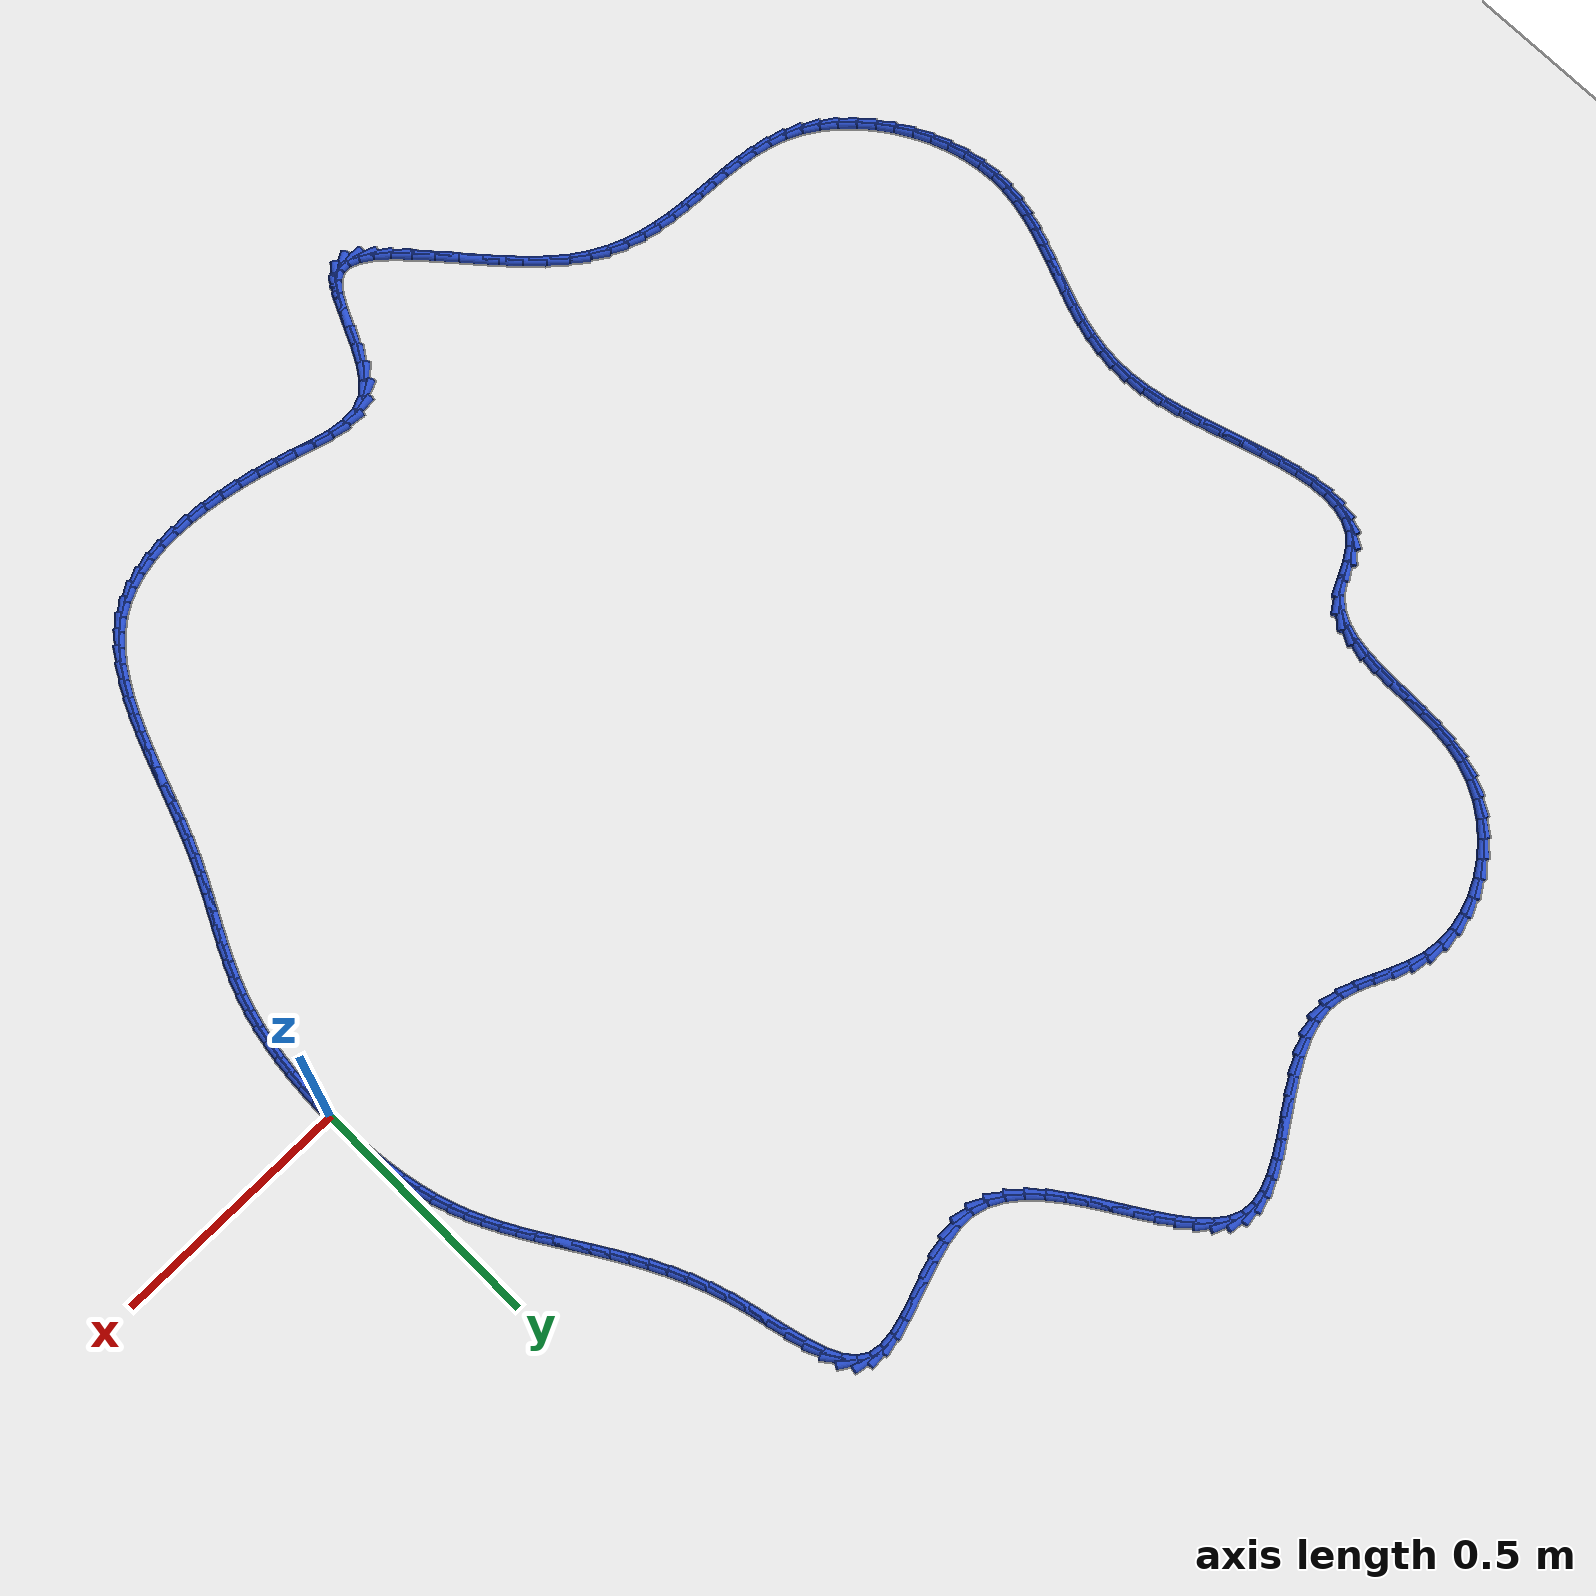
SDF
<sdf version="1.6">
 <world name="default">
  <light name="sun" type="directional">
   <pose>0 0 10 0 -0 0</pose>
   <diffuse>0.8 0.8 0.8 1</diffuse>
   <specular>0.2 0.2 0.2 1</specular>
   <attenuation>
    <range>1000</range>
    <constant>0.9</constant>
    <linear>0.01</linear>
    <quadratic>0.001</quadratic>
   </attenuation>
   <direction>-0.5 0.1 -0.9</direction>
  </light>
  <model name="ground_plane">
   <static>1</static>
   <link name="link">
    <collision name="collision">
     <geometry><plane><normal>0 0 1</normal><size>100 100</size></plane></geometry>
     <surface><friction><ode><mu>100</mu><mu2>50</mu2></ode></friction></surface>
    </collision>
    <visual name="visual">
     <cast_shadows>0</cast_shadows>
     <geometry><plane><normal>0 0 1</normal><size>100 100</size></plane></geometry>
     <material>
      <script><uri>file://media/materials/scripts/gazebo.material</uri><name>Gazebo/WhiteGlow</name></script>
     </material>
    </visual>
   </link>
  </model>
  <gravity>0 0 -9.8</gravity>
  <magnetic_field>6e-06 2.3e-05 -4.2e-05</magnetic_field>
  <atmosphere type="adiabatic"/>
  <physics name="default_physics" default="0" type="ode">
   <max_step_size>0.001</max_step_size>
   <real_time_factor>1</real_time_factor>
   <real_time_update_rate>1000</real_time_update_rate>
  </physics>
  <scene><ambient>0.4 0.4 0.4 1</ambient><background>0.7 0.7 0.7 1</background><shadows>1</shadows></scene>
  <spherical_coordinates>
   <surface_model>EARTH_WGS84</surface_model>
   <latitude_deg>0</latitude_deg>
   <longitude_deg>0</longitude_deg>
   <elevation>0</elevation>
   <heading_deg>0</heading_deg>
  </spherical_coordinates>
  <model name="line">
   <link name="link_0">
    <pose>3.469446951953614e-18 2.7755575615628914e-17 0.01 0 1.57 -1.556938290337987</pose>
    <collision name="collision">
     <geometry><cylinder><radius>0.01</radius><length>0.08</length></cylinder></geometry>
    </collision>
    <visual name="visual">
     <material>
      <script><name>Gazebo/Blue</name><uri>file://media/materials/scripts/gazebo.material</uri></script>
     </material>
     <geometry><cylinder><radius>0.01</radius><length>0.08</length></cylinder></geometry>
    </visual>
   </link>
   <link name="link_1">
    <pose>-0.0005086264192575455 0.03670028294934127 0.01 0 1.57 -1.526737304560786</pose>
    <collision name="collision">
     <geometry><cylinder><radius>0.01</radius><length>0.08</length></cylinder></geometry>
    </collision>
    <visual name="visual">
     <material>
      <script><name>Gazebo/Blue</name><uri>file://media/materials/scripts/gazebo.material</uri></script>
     </material>
     <geometry><cylinder><radius>0.01</radius><length>0.08</length></cylinder></geometry>
    </visual>
   </link>
   <link name="link_2">
    <pose>-0.0021235837073618974 0.0733309680475676 0.01 0 1.57 -1.4933308353421797</pose>
    <collision name="collision">
     <geometry><cylinder><radius>0.01</radius><length>0.08</length></cylinder></geometry>
    </collision>
    <visual name="visual">
     <material>
      <script><name>Gazebo/Blue</name><uri>file://media/materials/scripts/gazebo.material</uri></script>
     </material>
     <geometry><cylinder><radius>0.01</radius><length>0.08</length></cylinder></geometry>
    </visual>
   </link>
   <link name="link_3">
    <pose>-0.004949260395487355 0.10973456104645152 0.01 0 1.57 -1.456337692629741</pose>
    <collision name="collision">
     <geometry><cylinder><radius>0.01</radius><length>0.08</length></cylinder></geometry>
    </collision>
    <visual name="visual">
     <material>
      <script><name>Gazebo/Blue</name><uri>file://media/materials/scripts/gazebo.material</uri></script>
     </material>
     <geometry><cylinder><radius>0.01</radius><length>0.08</length></cylinder></geometry>
    </visual>
   </link>
   <link name="link_4">
    <pose>-0.009090045014808219 0.14575356769776568 0.01 0 1.57 -1.4153315411979794</pose>
    <collision name="collision">
     <geometry><cylinder><radius>0.01</radius><length>0.08</length></cylinder></geometry>
    </collision>
    <visual name="visual">
     <material>
      <script><name>Gazebo/Blue</name><uri>file://media/materials/scripts/gazebo.material</uri></script>
     </material>
     <geometry><cylinder><radius>0.01</radius><length>0.08</length></cylinder></geometry>
    </visual>
   </link>
   <link name="link_5">
    <pose>-0.014650326096498783 0.1812304937532826 0.01 0 1.57 -1.3698450771951134</pose>
    <collision name="collision">
     <geometry><cylinder><radius>0.01</radius><length>0.08</length></cylinder></geometry>
    </collision>
    <visual name="visual">
     <material>
      <script><name>Gazebo/Blue</name><uri>file://media/materials/scripts/gazebo.material</uri></script>
     </material>
     <geometry><cylinder><radius>0.01</radius><length>0.08</length></cylinder></geometry>
    </visual>
   </link>
   <link name="link_6">
    <pose>-0.021734492171733347 0.2160078449647749 0.01 0 1.57 -1.319380649504235</pose>
    <collision name="collision">
     <geometry><cylinder><radius>0.01</radius><length>0.08</length></cylinder></geometry>
    </collision>
    <visual name="visual">
     <material>
      <script><name>Gazebo/Blue</name><uri>file://media/materials/scripts/gazebo.material</uri></script>
     </material>
     <geometry><cylinder><radius>0.01</radius><length>0.08</length></cylinder></geometry>
    </visual>
   </link>
   <link name="link_7">
    <pose>-0.030446931771686215 0.24992812708401513 0.01 0 1.57 -1.263430914252035</pose>
    <collision name="collision">
     <geometry><cylinder><radius>0.01</radius><length>0.08</length></cylinder></geometry>
    </collision>
    <visual name="visual">
     <material>
      <script><name>Gazebo/Blue</name><uri>file://media/materials/scripts/gazebo.material</uri></script>
     </material>
     <geometry><cylinder><radius>0.01</radius><length>0.08</length></cylinder></geometry>
    </visual>
   </link>
   <link name="link_8">
    <pose>-0.040892031189807485 0.28283384830303826 0.01 0 1.57 -1.2039577810393982</pose>
    <collision name="collision">
     <geometry><cylinder><radius>0.01</radius><length>0.08</length></cylinder></geometry>
    </collision>
    <visual name="visual">
     <material>
      <script><name>Gazebo/Blue</name><uri>file://media/materials/scripts/gazebo.material</uri></script>
     </material>
     <geometry><cylinder><radius>0.01</radius><length>0.08</length></cylinder></geometry>
    </visual>
   </link>
   <link name="link_9">
    <pose>-0.053111385856684235 0.3146359909267199 0.01 0 1.57 -1.1500253934060036</pose>
    <collision name="collision">
     <geometry><cylinder><radius>0.01</radius><length>0.08</length></cylinder></geometry>
    </collision>
    <visual name="visual">
     <material>
      <script><name>Gazebo/Blue</name><uri>file://media/materials/scripts/gazebo.material</uri></script>
     </material>
     <geometry><cylinder><radius>0.01</radius><length>0.08</length></cylinder></geometry>
    </visual>
   </link>
   <link name="link_10">
    <pose>-0.06691977106962267 0.3454928870604103 0.01 0 1.57 -1.1045474351079927</pose>
    <collision name="collision">
     <geometry><cylinder><radius>0.01</radius><length>0.08</length></cylinder></geometry>
    </collision>
    <visual name="visual">
     <material>
      <script><name>Gazebo/Blue</name><uri>file://media/materials/scripts/gazebo.material</uri></script>
     </material>
     <geometry><cylinder><radius>0.01</radius><length>0.08</length></cylinder></geometry>
    </visual>
   </link>
   <link name="link_11">
    <pose>-0.08208076334813738 0.37561870162856725 0.01 0 1.57 -1.068153264390269</pose>
    <collision name="collision">
     <geometry><cylinder><radius>0.01</radius><length>0.08</length></cylinder></geometry>
    </collision>
    <visual name="visual">
     <material>
      <script><name>Gazebo/Blue</name><uri>file://media/materials/scripts/gazebo.material</uri></script>
     </material>
     <geometry><cylinder><radius>0.01</radius><length>0.08</length></cylinder></geometry>
    </visual>
   </link>
   <link name="link_12">
    <pose>-0.0983579392117429 0.4052275995556483 0.01 0 1.57 -1.0411528851741463</pose>
    <collision name="collision">
     <geometry><cylinder><radius>0.01</radius><length>0.08</length></cylinder></geometry>
    </collision>
    <visual name="visual">
     <material>
      <script><name>Gazebo/Blue</name><uri>file://media/materials/scripts/gazebo.material</uri></script>
     </material>
     <geometry><cylinder><radius>0.01</radius><length>0.08</length></cylinder></geometry>
    </visual>
   </link>
   <link name="link_13">
    <pose>-0.1155148751799537 0.43453374576611087 0.01 0 1.57 -1.0236162193588425</pose>
    <collision name="collision">
     <geometry><cylinder><radius>0.01</radius><length>0.08</length></cylinder></geometry>
    </collision>
    <visual name="visual">
     <material>
      <script><name>Gazebo/Blue</name><uri>file://media/materials/scripts/gazebo.material</uri></script>
     </material>
     <geometry><cylinder><radius>0.01</radius><length>0.08</length></cylinder></geometry>
    </visual>
   </link>
   <link name="link_14">
    <pose>-0.13331514777228431 0.4637513051844127 0.01 0 1.57 -1.0154451998023997</pose>
    <collision name="collision">
     <geometry><cylinder><radius>0.01</radius><length>0.08</length></cylinder></geometry>
    </collision>
    <visual name="visual">
     <material>
      <script><name>Gazebo/Blue</name><uri>file://media/materials/scripts/gazebo.material</uri></script>
     </material>
     <geometry><cylinder><radius>0.01</radius><length>0.08</length></cylinder></geometry>
    </visual>
   </link>
   <link name="link_15">
    <pose>-0.15152233350824934 0.4930944427350114 0.01 0 1.57 -1.0164265105368409</pose>
    <collision name="collision">
     <geometry><cylinder><radius>0.01</radius><length>0.08</length></cylinder></geometry>
    </collision>
    <visual name="visual">
     <material>
      <script><name>Gazebo/Blue</name><uri>file://media/materials/scripts/gazebo.material</uri></script>
     </material>
     <geometry><cylinder><radius>0.01</radius><length>0.08</length></cylinder></geometry>
    </visual>
   </link>
   <link name="link_16">
    <pose>-0.16990000890736318 0.5227773233423645 0.01 0 1.57 -1.0262610649358161</pose>
    <collision name="collision">
     <geometry><cylinder><radius>0.01</radius><length>0.08</length></cylinder></geometry>
    </collision>
    <visual name="visual">
     <material>
      <script><name>Gazebo/Blue</name><uri>file://media/materials/scripts/gazebo.material</uri></script>
     </material>
     <geometry><cylinder><radius>0.01</radius><length>0.08</length></cylinder></geometry>
    </visual>
   </link>
   <link name="link_17">
    <pose>-0.18821175048914052 0.5530141119309296 0.01 0 1.57 -1.0445716546282744</pose>
    <collision name="collision">
     <geometry><cylinder><radius>0.01</radius><length>0.08</length></cylinder></geometry>
    </collision>
    <visual name="visual">
     <material>
      <script><name>Gazebo/Blue</name><uri>file://media/materials/scripts/gazebo.material</uri></script>
     </material>
     <geometry><cylinder><radius>0.01</radius><length>0.08</length></cylinder></geometry>
    </visual>
   </link>
   <link name="link_18">
    <pose>-0.20622113477309573 0.5840189734251643 0.01 0 1.57 -1.0708933258021032</pose>
    <collision name="collision">
     <geometry><cylinder><radius>0.01</radius><length>0.08</length></cylinder></geometry>
    </collision>
    <visual name="visual">
     <material>
      <script><name>Gazebo/Blue</name><uri>file://media/materials/scripts/gazebo.material</uri></script>
     </material>
     <geometry><cylinder><radius>0.01</radius><length>0.08</length></cylinder></geometry>
    </visual>
   </link>
   <link name="link_19">
    <pose>-0.22369173827874345 0.6160060727495263 0.01 0 1.57 -1.104653052175301</pose>
    <collision name="collision">
     <geometry><cylinder><radius>0.01</radius><length>0.08</length></cylinder></geometry>
    </collision>
    <visual name="visual">
     <material>
      <script><name>Gazebo/Blue</name><uri>file://media/materials/scripts/gazebo.material</uri></script>
     </material>
     <geometry><cylinder><radius>0.01</radius><length>0.08</length></cylinder></geometry>
    </visual>
   </link>
   <link name="link_20">
    <pose>-0.24038713752559812 0.649189574828473 0.01 0 1.57 -1.14514684547393</pose>
    <collision name="collision">
     <geometry><cylinder><radius>0.01</radius><length>0.08</length></cylinder></geometry>
    </collision>
    <visual name="visual">
     <material>
      <script><name>Gazebo/Blue</name><uri>file://media/materials/scripts/gazebo.material</uri></script>
     </material>
     <geometry><cylinder><radius>0.01</radius><length>0.08</length></cylinder></geometry>
    </visual>
   </link>
   <link name="link_21">
    <pose>-0.25607090903317425 0.6837836445864618 0.01 0 1.57 -1.1915235009625469</pose>
    <collision name="collision">
     <geometry><cylinder><radius>0.01</radius><length>0.08</length></cylinder></geometry>
    </collision>
    <visual name="visual">
     <material>
      <script><name>Gazebo/Blue</name><uri>file://media/materials/scripts/gazebo.material</uri></script>
     </material>
     <geometry><cylinder><radius>0.01</radius><length>0.08</length></cylinder></geometry>
    </visual>
   </link>
   <link name="link_22">
    <pose>-0.27050662932098646 0.7200024469479507 0.01 0 1.57 -1.2427839783461925</pose>
    <collision name="collision">
     <geometry><cylinder><radius>0.01</radius><length>0.08</length></cylinder></geometry>
    </collision>
    <visual name="visual">
     <material>
      <script><name>Gazebo/Blue</name><uri>file://media/materials/scripts/gazebo.material</uri></script>
     </material>
     <geometry><cylinder><radius>0.01</radius><length>0.08</length></cylinder></geometry>
    </visual>
   </link>
   <link name="link_23">
    <pose>-0.2834578749085493 0.7580601468373972 0.01 0 1.57 -1.2970016770641377</pose>
    <collision name="collision">
     <geometry><cylinder><radius>0.01</radius><length>0.08</length></cylinder></geometry>
    </collision>
    <visual name="visual">
     <material>
      <script><name>Gazebo/Blue</name><uri>file://media/materials/scripts/gazebo.material</uri></script>
     </material>
     <geometry><cylinder><radius>0.01</radius><length>0.08</length></cylinder></geometry>
    </visual>
   </link>
   <link name="link_24">
    <pose>-0.29471231918555835 0.7981332619435436 0.01 0 1.57 -1.3354436142135362</pose>
    <collision name="collision">
     <geometry><cylinder><radius>0.01</radius><length>0.08</length></cylinder></geometry>
    </collision>
    <visual name="visual">
     <material>
      <script><name>Gazebo/Blue</name><uri>file://media/materials/scripts/gazebo.material</uri></script>
     </material>
     <geometry><cylinder><radius>0.01</radius><length>0.08</length></cylinder></geometry>
    </visual>
   </link>
   <link name="link_25">
    <pose>-0.30463211362388926 0.8395007862680156 0.01 0 1.57 -1.3424743260878873</pose>
    <collision name="collision">
     <geometry><cylinder><radius>0.01</radius><length>0.08</length></cylinder></geometry>
    </collision>
    <visual name="visual">
     <material>
      <script><name>Gazebo/Blue</name><uri>file://media/materials/scripts/gazebo.material</uri></script>
     </material>
     <geometry><cylinder><radius>0.01</radius><length>0.08</length></cylinder></geometry>
    </visual>
   </link>
   <link name="link_26">
    <pose>-0.3141653682346374 0.8805262538759628 0.01 0 1.57 -1.316915009802149</pose>
    <collision name="collision">
     <geometry><cylinder><radius>0.01</radius><length>0.08</length></cylinder></geometry>
    </collision>
    <visual name="visual">
     <material>
      <script><name>Gazebo/Blue</name><uri>file://media/materials/scripts/gazebo.material</uri></script>
     </material>
     <geometry><cylinder><radius>0.01</radius><length>0.08</length></cylinder></geometry>
    </visual>
   </link>
   <link name="link_27">
    <pose>-0.3242865862723072 0.9195319639066547 0.01 0 1.57 -1.2512326649928887</pose>
    <collision name="collision">
     <geometry><cylinder><radius>0.01</radius><length>0.08</length></cylinder></geometry>
    </collision>
    <visual name="visual">
     <material>
      <script><name>Gazebo/Blue</name><uri>file://media/materials/scripts/gazebo.material</uri></script>
     </material>
     <geometry><cylinder><radius>0.01</radius><length>0.08</length></cylinder></geometry>
    </visual>
   </link>
   <link name="link_28">
    <pose>-0.3359702709914028 0.95484021549936 0.01 0 1.57 -1.1272815975000887</pose>
    <collision name="collision">
     <geometry><cylinder><radius>0.01</radius><length>0.08</length></cylinder></geometry>
    </collision>
    <visual name="visual">
     <material>
      <script><name>Gazebo/Blue</name><uri>file://media/materials/scripts/gazebo.material</uri></script>
     </material>
     <geometry><cylinder><radius>0.01</radius><length>0.08</length></cylinder></geometry>
    </visual>
   </link>
   <link name="link_29">
    <pose>-0.35019092564642823 0.9847733077933484 0.01 0 1.57 -0.9114876799549118</pose>
    <collision name="collision">
     <geometry><cylinder><radius>0.01</radius><length>0.08</length></cylinder></geometry>
    </collision>
    <visual name="visual">
     <material>
      <script><name>Gazebo/Blue</name><uri>file://media/materials/scripts/gazebo.material</uri></script>
     </material>
     <geometry><cylinder><radius>0.01</radius><length>0.08</length></cylinder></geometry>
    </visual>
   </link>
   <link name="link_30">
    <pose>-0.3679230534918876 1.0076535399278885 0.01 0 1.57 -0.5674269223670447</pose>
    <collision name="collision">
     <geometry><cylinder><radius>0.01</radius><length>0.08</length></cylinder></geometry>
    </collision>
    <visual name="visual">
     <material>
      <script><name>Gazebo/Blue</name><uri>file://media/materials/scripts/gazebo.material</uri></script>
     </material>
     <geometry><cylinder><radius>0.01</radius><length>0.08</length></cylinder></geometry>
    </visual>
   </link>
   <link name="link_31">
    <pose>-0.39013700569453613 1.0218114761537689 0.01 0 1.57 -0.17878044460456757</pose>
    <collision name="collision">
     <geometry><cylinder><radius>0.01</radius><length>0.08</length></cylinder></geometry>
    </collision>
    <visual name="visual">
     <material>
      <script><name>Gazebo/Blue</name><uri>file://media/materials/scripts/gazebo.material</uri></script>
     </material>
     <geometry><cylinder><radius>0.01</radius><length>0.08</length></cylinder></geometry>
    </visual>
   </link>
   <link name="link_32">
    <pose>-0.4172351157093001 1.0267083720792871 0.01 0 1.57 0.08406990753217967</pose>
    <collision name="collision">
     <geometry><cylinder><radius>0.01</radius><length>0.08</length></cylinder></geometry>
    </collision>
    <visual name="visual">
     <material>
      <script><name>Gazebo/Blue</name><uri>file://media/materials/scripts/gazebo.material</uri></script>
     </material>
     <geometry><cylinder><radius>0.01</radius><length>0.08</length></cylinder></geometry>
    </visual>
   </link>
   <link name="link_33">
    <pose>-0.4484793615662948 1.02407546538631 0.01 0 1.57 0.23215058015567583</pose>
    <collision name="collision">
     <geometry><cylinder><radius>0.01</radius><length>0.08</length></cylinder></geometry>
    </collision>
    <visual name="visual">
     <material>
      <script><name>Gazebo/Blue</name><uri>file://media/materials/scripts/gazebo.material</uri></script>
     </material>
     <geometry><cylinder><radius>0.01</radius><length>0.08</length></cylinder></geometry>
    </visual>
   </link>
   <link name="link_34">
    <pose>-0.4829953591120713 1.015915435191075 0.01 0 1.57 0.3065591736147325</pose>
    <collision name="collision">
     <geometry><cylinder><radius>0.01</radius><length>0.08</length></cylinder></geometry>
    </collision>
    <visual name="visual">
     <material>
      <script><name>Gazebo/Blue</name><uri>file://media/materials/scripts/gazebo.material</uri></script>
     </material>
     <geometry><cylinder><radius>0.01</radius><length>0.08</length></cylinder></geometry>
    </visual>
   </link>
   <link name="link_35">
    <pose>-0.5199087241931807 1.0042309606098208 0.01 0 1.57 0.33095053188766144</pose>
    <collision name="collision">
     <geometry><cylinder><radius>0.01</radius><length>0.08</length></cylinder></geometry>
    </collision>
    <visual name="visual">
     <material>
      <script><name>Gazebo/Blue</name><uri>file://media/materials/scripts/gazebo.material</uri></script>
     </material>
     <geometry><cylinder><radius>0.01</radius><length>0.08</length></cylinder></geometry>
    </visual>
   </link>
   <link name="link_36">
    <pose>-0.5583450726561742 0.9910247207587847 0.01 0 1.57 0.3147575271745641</pose>
    <collision name="collision">
     <geometry><cylinder><radius>0.01</radius><length>0.08</length></cylinder></geometry>
    </collision>
    <visual name="visual">
     <material>
      <script><name>Gazebo/Blue</name><uri>file://media/materials/scripts/gazebo.material</uri></script>
     </material>
     <geometry><cylinder><radius>0.01</radius><length>0.08</length></cylinder></geometry>
    </visual>
   </link>
   <link name="link_37">
    <pose>-0.5974300203476028 0.9782993947542048 0.01 0 1.57 0.2577000311489832</pose>
    <collision name="collision">
     <geometry><cylinder><radius>0.01</radius><length>0.08</length></cylinder></geometry>
    </collision>
    <visual name="visual">
     <material>
      <script><name>Gazebo/Blue</name><uri>file://media/materials/scripts/gazebo.material</uri></script>
     </material>
     <geometry><cylinder><radius>0.01</radius><length>0.08</length></cylinder></geometry>
    </visual>
   </link>
   <link name="link_38">
    <pose>-0.6362891831140176 0.9680576617123192 0.01 0 1.57 0.1512619375611397</pose>
    <collision name="collision">
     <geometry><cylinder><radius>0.01</radius><length>0.08</length></cylinder></geometry>
    </collision>
    <visual name="visual">
     <material>
      <script><name>Gazebo/Blue</name><uri>file://media/materials/scripts/gazebo.material</uri></script>
     </material>
     <geometry><cylinder><radius>0.01</radius><length>0.08</length></cylinder></geometry>
    </visual>
   </link>
   <link name="link_39">
    <pose>-0.6740481768019697 0.9623022007493656 0.01 0 1.57 -0.02049459274574224</pose>
    <collision name="collision">
     <geometry><cylinder><radius>0.01</radius><length>0.08</length></cylinder></geometry>
    </collision>
    <visual name="visual">
     <material>
      <script><name>Gazebo/Blue</name><uri>file://media/materials/scripts/gazebo.material</uri></script>
     </material>
     <geometry><cylinder><radius>0.01</radius><length>0.08</length></cylinder></geometry>
    </visual>
   </link>
   <link name="link_40">
    <pose>-0.70983261725801 0.9630356909815817 0.01 0 1.57 -0.25971051715296517</pose>
    <collision name="collision">
     <geometry><cylinder><radius>0.01</radius><length>0.08</length></cylinder></geometry>
    </collision>
    <visual name="visual">
     <material>
      <script><name>Gazebo/Blue</name><uri>file://media/materials/scripts/gazebo.material</uri></script>
     </material>
     <geometry><cylinder><radius>0.01</radius><length>0.08</length></cylinder></geometry>
    </visual>
   </link>
   <link name="link_41">
    <pose>-0.7429300852464396 0.9718300720499317 0.01 0 1.57 -0.4906222337918339</pose>
    <collision name="collision">
     <geometry><cylinder><radius>0.01</radius><length>0.08</length></cylinder></geometry>
    </collision>
    <visual name="visual">
     <material>
      <script><name>Gazebo/Blue</name><uri>file://media/materials/scripts/gazebo.material</uri></script>
     </material>
     <geometry><cylinder><radius>0.01</radius><length>0.08</length></cylinder></geometry>
    </visual>
   </link>
   <link name="link_42">
    <pose>-0.7734306495558869 0.9881230975301817 0.01 0 1.57 -0.6742269239058732</pose>
    <collision name="collision">
     <geometry><cylinder><radius>0.01</radius><length>0.08</length></cylinder></geometry>
    </collision>
    <visual name="visual">
     <material>
      <script><name>Gazebo/Blue</name><uri>file://media/materials/scripts/gazebo.material</uri></script>
     </material>
     <geometry><cylinder><radius>0.01</radius><length>0.08</length></cylinder></geometry>
    </visual>
   </link>
   <link name="link_43">
    <pose>-0.8016724631631442 1.0106927506322785 0.01 0 1.57 -0.8095434952781009</pose>
    <collision name="collision">
     <geometry><cylinder><radius>0.01</radius><length>0.08</length></cylinder></geometry>
    </collision>
    <visual name="visual">
     <material>
      <script><name>Gazebo/Blue</name><uri>file://media/materials/scripts/gazebo.material</uri></script>
     </material>
     <geometry><cylinder><radius>0.01</radius><length>0.08</length></cylinder></geometry>
    </visual>
   </link>
   <link name="link_44">
    <pose>-0.8279937518074563 1.038316821057225 0.01 0 1.57 -0.9043684336429197</pose>
    <collision name="collision">
     <geometry><cylinder><radius>0.01</radius><length>0.08</length></cylinder></geometry>
    </collision>
    <visual name="visual">
     <material>
      <script><name>Gazebo/Blue</name><uri>file://media/materials/scripts/gazebo.material</uri></script>
     </material>
     <geometry><cylinder><radius>0.01</radius><length>0.08</length></cylinder></geometry>
    </visual>
   </link>
   <link name="link_45">
    <pose>-0.8527327412280671 1.069773098506022 0.01 0 1.57 -0.9670284186279875</pose>
    <collision name="collision">
     <geometry><cylinder><radius>0.01</radius><length>0.08</length></cylinder></geometry>
    </collision>
    <visual name="visual">
     <material>
      <script><name>Gazebo/Blue</name><uri>file://media/materials/scripts/gazebo.material</uri></script>
     </material>
     <geometry><cylinder><radius>0.01</radius><length>0.08</length></cylinder></geometry>
    </visual>
   </link>
   <link name="link_46">
    <pose>-0.8762276571642211 1.1038393726796731 0.01 0 1.57 -1.0035173630592025</pose>
    <collision name="collision">
     <geometry><cylinder><radius>0.01</radius><length>0.08</length></cylinder></geometry>
    </collision>
    <visual name="visual">
     <material>
      <script><name>Gazebo/Blue</name><uri>file://media/materials/scripts/gazebo.material</uri></script>
     </material>
     <geometry><cylinder><radius>0.01</radius><length>0.08</length></cylinder></geometry>
    </visual>
   </link>
   <link name="link_47">
    <pose>-0.8988167253551628 1.1392934332791795 0.01 0 1.57 -1.0170736828147484</pose>
    <collision name="collision">
     <geometry><cylinder><radius>0.01</radius><length>0.08</length></cylinder></geometry>
    </collision>
    <visual name="visual">
     <material>
      <script><name>Gazebo/Blue</name><uri>file://media/materials/scripts/gazebo.material</uri></script>
     </material>
     <geometry><cylinder><radius>0.01</radius><length>0.08</length></cylinder></geometry>
    </visual>
   </link>
   <link name="link_48">
    <pose>-0.9208381715401365 1.1749130700055441 0.01 0 1.57 -1.0082501380490017</pose>
    <collision name="collision">
     <geometry><cylinder><radius>0.01</radius><length>0.08</length></cylinder></geometry>
    </collision>
    <visual name="visual">
     <material>
      <script><name>Gazebo/Blue</name><uri>file://media/materials/scripts/gazebo.material</uri></script>
     </material>
     <geometry><cylinder><radius>0.01</radius><length>0.08</length></cylinder></geometry>
    </visual>
   </link>
   <link name="link_49">
    <pose>-0.9426302214583865 1.2094760725597689 0.01 0 1.57 -0.9747292847209108</pose>
    <collision name="collision">
     <geometry><cylinder><radius>0.01</radius><length>0.08</length></cylinder></geometry>
    </collision>
    <visual name="visual">
     <material>
      <script><name>Gazebo/Blue</name><uri>file://media/materials/scripts/gazebo.material</uri></script>
     </material>
     <geometry><cylinder><radius>0.01</radius><length>0.08</length></cylinder></geometry>
    </visual>
   </link>
   <link name="link_50">
    <pose>-0.9645311008491572 1.2417602306428557 0.01 0 1.57 -0.9105963002312113</pose>
    <collision name="collision">
     <geometry><cylinder><radius>0.01</radius><length>0.08</length></cylinder></geometry>
    </collision>
    <visual name="visual">
     <material>
      <script><name>Gazebo/Blue</name><uri>file://media/materials/scripts/gazebo.material</uri></script>
     </material>
     <geometry><cylinder><radius>0.01</radius><length>0.08</length></cylinder></geometry>
    </visual>
   </link>
   <link name="link_51">
    <pose>-0.9868790354516932 1.2705433339558068 0.01 0 1.57 -0.8050303669804222</pose>
    <collision name="collision">
     <geometry><cylinder><radius>0.01</radius><length>0.08</length></cylinder></geometry>
    </collision>
    <visual name="visual">
     <material>
      <script><name>Gazebo/Blue</name><uri>file://media/materials/scripts/gazebo.material</uri></script>
     </material>
     <geometry><cylinder><radius>0.01</radius><length>0.08</length></cylinder></geometry>
    </visual>
   </link>
   <link name="link_52">
    <pose>-1.0100122510052385 1.2946031721996245 0.01 0 1.57 -0.6414352117856895</pose>
    <collision name="collision">
     <geometry><cylinder><radius>0.01</radius><length>0.08</length></cylinder></geometry>
    </collision>
    <visual name="visual">
     <material>
      <script><name>Gazebo/Blue</name><uri>file://media/materials/scripts/gazebo.material</uri></script>
     </material>
     <geometry><cylinder><radius>0.01</radius><length>0.08</length></cylinder></geometry>
    </visual>
   </link>
   <link name="link_53">
    <pose>-1.0342689732490378 1.3127175350753113 0.01 0 1.57 -0.402408465834181</pose>
    <collision name="collision">
     <geometry><cylinder><radius>0.01</radius><length>0.08</length></cylinder></geometry>
    </collision>
    <visual name="visual">
     <material>
      <script><name>Gazebo/Blue</name><uri>file://media/materials/scripts/gazebo.material</uri></script>
     </material>
     <geometry><cylinder><radius>0.01</radius><length>0.08</length></cylinder></geometry>
    </visual>
   </link>
   <link name="link_54">
    <pose>-1.0599874279223354 1.323664212283869 0.01 0 1.57 -0.09982717758484334</pose>
    <collision name="collision">
     <geometry><cylinder><radius>0.01</radius><length>0.08</length></cylinder></geometry>
    </collision>
    <visual name="visual">
     <material>
      <script><name>Gazebo/Blue</name><uri>file://media/materials/scripts/gazebo.material</uri></script>
     </material>
     <geometry><cylinder><radius>0.01</radius><length>0.08</length></cylinder></geometry>
    </visual>
   </link>
   <link name="link_55">
    <pose>-1.0874645526092437 1.3264163241942417 0.01 0 1.57 0.16464403361150992</pose>
    <collision name="collision">
     <geometry><cylinder><radius>0.01</radius><length>0.08</length></cylinder></geometry>
    </collision>
    <visual name="visual">
     <material>
      <script><name>Gazebo/Blue</name><uri>file://media/materials/scripts/gazebo.material</uri></script>
     </material>
     <geometry><cylinder><radius>0.01</radius><length>0.08</length></cylinder></geometry>
    </visual>
   </link>
   <link name="link_56">
    <pose>-1.1166549831075208 1.321566391130453 0.01 0 1.57 0.34586061049891365</pose>
    <collision name="collision">
     <geometry><cylinder><radius>0.01</radius><length>0.08</length></cylinder></geometry>
    </collision>
    <visual name="visual">
     <material>
      <script><name>Gazebo/Blue</name><uri>file://media/materials/scripts/gazebo.material</uri></script>
     </material>
     <geometry><cylinder><radius>0.01</radius><length>0.08</length></cylinder></geometry>
    </visual>
   </link>
   <link name="link_57">
    <pose>-1.147344084330397 1.3105077392368027 0.01 0 1.57 0.4607003016405857</pose>
    <collision name="collision">
     <geometry><cylinder><radius>0.01</radius><length>0.08</length></cylinder></geometry>
    </collision>
    <visual name="visual">
     <material>
      <script><name>Gazebo/Blue</name><uri>file://media/materials/scripts/gazebo.material</uri></script>
     </material>
     <geometry><cylinder><radius>0.01</radius><length>0.08</length></cylinder></geometry>
    </visual>
   </link>
   <link name="link_58">
    <pose>-1.1793160176548019 1.2946393884830552 0.01 0 1.57 0.5282172132101465</pose>
    <collision name="collision">
     <geometry><cylinder><radius>0.01</radius><length>0.08</length></cylinder></geometry>
    </collision>
    <visual name="visual">
     <material>
      <script><name>Gazebo/Blue</name><uri>file://media/materials/scripts/gazebo.material</uri></script>
     </material>
     <geometry><cylinder><radius>0.01</radius><length>0.08</length></cylinder></geometry>
    </visual>
   </link>
   <link name="link_59">
    <pose>-1.2123549444576678 1.2753603588389746 0.01 0 1.57 0.5609170025685546</pose>
    <collision name="collision">
     <geometry><cylinder><radius>0.01</radius><length>0.08</length></cylinder></geometry>
    </collision>
    <visual name="visual">
     <material>
      <script><name>Gazebo/Blue</name><uri>file://media/materials/scripts/gazebo.material</uri></script>
     </material>
     <geometry><cylinder><radius>0.01</radius><length>0.08</length></cylinder></geometry>
    </visual>
   </link>
   <link name="link_60">
    <pose>-1.2462450261159246 1.254069670274325 0.01 0 1.57 0.5653388998060731</pose>
    <collision name="collision">
     <geometry><cylinder><radius>0.01</radius><length>0.08</length></cylinder></geometry>
    </collision>
    <visual name="visual">
     <material>
      <script><name>Gazebo/Blue</name><uri>file://media/materials/scripts/gazebo.material</uri></script>
     </material>
     <geometry><cylinder><radius>0.01</radius><length>0.08</length></cylinder></geometry>
    </visual>
   </link>
   <link name="link_61">
    <pose>-1.2807704240065036 1.23216634275887 0.01 0 1.57 0.5435701999124434</pose>
    <collision name="collision">
     <geometry><cylinder><radius>0.01</radius><length>0.08</length></cylinder></geometry>
    </collision>
    <visual name="visual">
     <material>
      <script><name>Gazebo/Blue</name><uri>file://media/materials/scripts/gazebo.material</uri></script>
     </material>
     <geometry><cylinder><radius>0.01</radius><length>0.08</length></cylinder></geometry>
    </visual>
   </link>
   <link name="link_62">
    <pose>-1.3157152995063355 1.2110493962623747 0.01 0 1.57 0.4940609550055763</pose>
    <collision name="collision">
     <geometry><cylinder><radius>0.01</radius><length>0.08</length></cylinder></geometry>
    </collision>
    <visual name="visual">
     <material>
      <script><name>Gazebo/Blue</name><uri>file://media/materials/scripts/gazebo.material</uri></script>
     </material>
     <geometry><cylinder><radius>0.01</radius><length>0.08</length></cylinder></geometry>
    </visual>
   </link>
   <link name="link_63">
    <pose>-1.3508638139923517 1.1921178507546024 0.01 0 1.57 0.4118127644955454</pose>
    <collision name="collision">
     <geometry><cylinder><radius>0.01</radius><length>0.08</length></cylinder></geometry>
    </collision>
    <visual name="visual">
     <material>
      <script><name>Gazebo/Blue</name><uri>file://media/materials/scripts/gazebo.material</uri></script>
     </material>
     <geometry><cylinder><radius>0.01</radius><length>0.08</length></cylinder></geometry>
    </visual>
   </link>
   <link name="link_64">
    <pose>-1.3860001288414825 1.176770726205318 0.01 0 1.57 0.28859497038842274</pose>
    <collision name="collision">
     <geometry><cylinder><radius>0.01</radius><length>0.08</length></cylinder></geometry>
    </collision>
    <visual name="visual">
     <material>
      <script><name>Gazebo/Blue</name><uri>file://media/materials/scripts/gazebo.material</uri></script>
     </material>
     <geometry><cylinder><radius>0.01</radius><length>0.08</length></cylinder></geometry>
    </visual>
   </link>
   <link name="link_65">
    <pose>-1.4209084054306593 1.1664070425842852 0.01 0 1.57 0.11500721039546787</pose>
    <collision name="collision">
     <geometry><cylinder><radius>0.01</radius><length>0.08</length></cylinder></geometry>
    </collision>
    <visual name="visual">
     <material>
      <script><name>Gazebo/Blue</name><uri>file://media/materials/scripts/gazebo.material</uri></script>
     </material>
     <geometry><cylinder><radius>0.01</radius><length>0.08</length></cylinder></geometry>
    </visual>
   </link>
   <link name="link_66">
    <pose>-1.4553728051368124 1.1624258198612671 0.01 0 1.57 -0.10520899492809196</pose>
    <collision name="collision">
     <geometry><cylinder><radius>0.01</radius><length>0.08</length></cylinder></geometry>
    </collision>
    <visual name="visual">
     <material>
      <script><name>Gazebo/Blue</name><uri>file://media/materials/scripts/gazebo.material</uri></script>
     </material>
     <geometry><cylinder><radius>0.01</radius><length>0.08</length></cylinder></geometry>
    </visual>
   </link>
   <link name="link_67">
    <pose>-1.4892094859385194 1.1659989363072776 0.01 0 1.57 -0.29095171063610425</pose>
    <collision name="collision">
     <geometry><cylinder><radius>0.01</radius><length>0.08</length></cylinder></geometry>
    </collision>
    <visual name="visual">
     <material>
      <script><name>Gazebo/Blue</name><uri>file://media/materials/scripts/gazebo.material</uri></script>
     </material>
     <geometry><cylinder><radius>0.01</radius><length>0.08</length></cylinder></geometry>
    </visual>
   </link>
   <link name="link_68">
    <pose>-1.522560349608142 1.1759858371575802 0.01 0 1.57 -0.3968031191720669</pose>
    <collision name="collision">
     <geometry><cylinder><radius>0.01</radius><length>0.08</length></cylinder></geometry>
    </collision>
    <visual name="visual">
     <material>
      <script><name>Gazebo/Blue</name><uri>file://media/materials/scripts/gazebo.material</uri></script>
     </material>
     <geometry><cylinder><radius>0.01</radius><length>0.08</length></cylinder></geometry>
    </visual>
   </link>
   <link name="link_69">
    <pose>-1.5557574066739857 1.1898963985197284 0.01 0 1.57 -0.430483257738452</pose>
    <collision name="collision">
     <geometry><cylinder><radius>0.01</radius><length>0.08</length></cylinder></geometry>
    </collision>
    <visual name="visual">
     <material>
      <script><name>Gazebo/Blue</name><uri>file://media/materials/scripts/gazebo.material</uri></script>
     </material>
     <geometry><cylinder><radius>0.01</radius><length>0.08</length></cylinder></geometry>
    </visual>
   </link>
   <link name="link_70">
    <pose>-1.589135046029348 1.2052236126499996 0.01 0 1.57 -0.39767721714755344</pose>
    <collision name="collision">
     <geometry><cylinder><radius>0.01</radius><length>0.08</length></cylinder></geometry>
    </collision>
    <visual name="visual">
     <material>
      <script><name>Gazebo/Blue</name><uri>file://media/materials/scripts/gazebo.material</uri></script>
     </material>
     <geometry><cylinder><radius>0.01</radius><length>0.08</length></cylinder></geometry>
    </visual>
   </link>
   <link name="link_71">
    <pose>-1.6230276565675221 1.2194604718046695 0.01 0 1.57 -0.29717472348617013</pose>
    <collision name="collision">
     <geometry><cylinder><radius>0.01</radius><length>0.08</length></cylinder></geometry>
    </collision>
    <visual name="visual">
     <material>
      <script><name>Gazebo/Blue</name><uri>file://media/materials/scripts/gazebo.material</uri></script>
     </material>
     <geometry><cylinder><radius>0.01</radius><length>0.08</length></cylinder></geometry>
    </visual>
   </link>
   <link name="link_72">
    <pose>-1.6577696271818045 1.2300999682400158 0.01 0 1.57 -0.13508129840582114</pose>
    <collision name="collision">
     <geometry><cylinder><radius>0.01</radius><length>0.08</length></cylinder></geometry>
    </collision>
    <visual name="visual">
     <material>
      <script><name>Gazebo/Blue</name><uri>file://media/materials/scripts/gazebo.material</uri></script>
     </material>
     <geometry><cylinder><radius>0.01</radius><length>0.08</length></cylinder></geometry>
    </visual>
   </link>
   <link name="link_73">
    <pose>-1.6935872632900912 1.2349679054588667 0.01 0 1.57 0.03197174831315225</pose>
    <collision name="collision">
     <geometry><cylinder><radius>0.01</radius><length>0.08</length></cylinder></geometry>
    </collision>
    <visual name="visual">
     <material>
      <script><name>Gazebo/Blue</name><uri>file://media/materials/scripts/gazebo.material</uri></script>
     </material>
     <geometry><cylinder><radius>0.01</radius><length>0.08</length></cylinder></geometry>
    </visual>
   </link>
   <link name="link_74">
    <pose>-1.7300864249963273 1.2338005656713136 0.01 0 1.57 0.18349414591373775</pose>
    <collision name="collision">
     <geometry><cylinder><radius>0.01</radius><length>0.08</length></cylinder></geometry>
    </collision>
    <visual name="visual">
     <material>
      <script><name>Gazebo/Blue</name><uri>file://media/materials/scripts/gazebo.material</uri></script>
     </material>
     <geometry><cylinder><radius>0.01</radius><length>0.08</length></cylinder></geometry>
    </visual>
   </link>
   <link name="link_75">
    <pose>-1.7666519951653212 1.2270146654475056 0.01 0 1.57 0.3212852747612042</pose>
    <collision name="collision">
     <geometry><cylinder><radius>0.01</radius><length>0.08</length></cylinder></geometry>
    </collision>
    <visual name="visual">
     <material>
      <script><name>Gazebo/Blue</name><uri>file://media/materials/scripts/gazebo.material</uri></script>
     </material>
     <geometry><cylinder><radius>0.01</radius><length>0.08</length></cylinder></geometry>
    </visual>
   </link>
   <link name="link_76">
    <pose>-1.8026685869960055 1.2150277517142882 0.01 0 1.57 0.4484829018805257</pose>
    <collision name="collision">
     <geometry><cylinder><radius>0.01</radius><length>0.08</length></cylinder></geometry>
    </collision>
    <visual name="visual">
     <material>
      <script><name>Gazebo/Blue</name><uri>file://media/materials/scripts/gazebo.material</uri></script>
     </material>
     <geometry><cylinder><radius>0.01</radius><length>0.08</length></cylinder></geometry>
    </visual>
   </link>
   <link name="link_77">
    <pose>-1.8375208136873113 1.1982573713985074 0.01 0 1.57 0.5686676105384731</pose>
    <collision name="collision">
     <geometry><cylinder><radius>0.01</radius><length>0.08</length></cylinder></geometry>
    </collision>
    <visual name="visual">
     <material>
      <script><name>Gazebo/Blue</name><uri>file://media/materials/scripts/gazebo.material</uri></script>
     </material>
     <geometry><cylinder><radius>0.01</radius><length>0.08</length></cylinder></geometry>
    </visual>
   </link>
   <link name="link_78">
    <pose>-1.8705932884381704 1.1771210714270073 0.01 0 1.57 0.6854372157209035</pose>
    <collision name="collision">
     <geometry><cylinder><radius>0.01</radius><length>0.08</length></cylinder></geometry>
    </collision>
    <visual name="visual">
     <material>
      <script><name>Gazebo/Blue</name><uri>file://media/materials/scripts/gazebo.material</uri></script>
     </material>
     <geometry><cylinder><radius>0.01</radius><length>0.08</length></cylinder></geometry>
    </visual>
   </link>
   <link name="link_79">
    <pose>-1.901270624447514 1.1520363987266333 0.01 0 1.57 0.8022524506681019</pose>
    <collision name="collision">
     <geometry><cylinder><radius>0.01</radius><length>0.08</length></cylinder></geometry>
    </collision>
    <visual name="visual">
     <material>
      <script><name>Gazebo/Blue</name><uri>file://media/materials/scripts/gazebo.material</uri></script>
     </material>
     <geometry><cylinder><radius>0.01</radius><length>0.08</length></cylinder></geometry>
    </visual>
   </link>
   <link name="link_80">
    <pose>-1.9289374349142732 1.1234209002242297 0.01 0 1.57 0.9223853341117962</pose>
    <collision name="collision">
     <geometry><cylinder><radius>0.01</radius><length>0.08</length></cylinder></geometry>
    </collision>
    <visual name="visual">
     <material>
      <script><name>Gazebo/Blue</name><uri>file://media/materials/scripts/gazebo.material</uri></script>
     </material>
     <geometry><cylinder><radius>0.01</radius><length>0.08</length></cylinder></geometry>
    </visual>
   </link>
   <link name="link_81">
    <pose>-1.9529783330373807 1.0916921228466434 0.01 0 1.57 1.0488418504591033</pose>
    <collision name="collision">
     <geometry><cylinder><radius>0.01</radius><length>0.08</length></cylinder></geometry>
    </collision>
    <visual name="visual">
     <material>
      <script><name>Gazebo/Blue</name><uri>file://media/materials/scripts/gazebo.material</uri></script>
     </material>
     <geometry><cylinder><radius>0.01</radius><length>0.08</length></cylinder></geometry>
    </visual>
   </link>
   <link name="link_82">
    <pose>-1.9727779320157661 1.0572676135207173 0.01 0 1.57 1.1840933940776888</pose>
    <collision name="collision">
     <geometry><cylinder><radius>0.01</radius><length>0.08</length></cylinder></geometry>
    </collision>
    <visual name="visual">
     <material>
      <script><name>Gazebo/Blue</name><uri>file://media/materials/scripts/gazebo.material</uri></script>
     </material>
     <geometry><cylinder><radius>0.01</radius><length>0.08</length></cylinder></geometry>
    </visual>
   </link>
   <link name="link_83">
    <pose>-1.987723377277526 1.0205651906223883 0.01 0 1.57 1.317220983208514</pose>
    <collision name="collision">
     <geometry><cylinder><radius>0.01</radius><length>0.08</length></cylinder></geometry>
    </collision>
    <visual name="visual">
     <material>
      <script><name>Gazebo/Blue</name><uri>file://media/materials/scripts/gazebo.material</uri></script>
     </material>
     <geometry><cylinder><radius>0.01</radius><length>0.08</length></cylinder></geometry>
    </visual>
   </link>
   <link name="link_84">
    <pose>-1.9977030776985634 0.9820564068062303 0.01 0 1.57 1.4208002400702815</pose>
    <collision name="collision">
     <geometry><cylinder><radius>0.01</radius><length>0.08</length></cylinder></geometry>
    </collision>
    <visual name="visual">
     <material>
      <script><name>Gazebo/Blue</name><uri>file://media/materials/scripts/gazebo.material</uri></script>
     </material>
     <geometry><cylinder><radius>0.01</radius><length>0.08</length></cylinder></geometry>
    </visual>
   </link>
   <link name="link_85">
    <pose>-2.0037068444693786 0.9423308824996054 0.01 0 1.57 1.492515523894807</pose>
    <collision name="collision">
     <geometry><cylinder><radius>0.01</radius><length>0.08</length></cylinder></geometry>
    </collision>
    <visual name="visual">
     <material>
      <script><name>Gazebo/Blue</name><uri>file://media/materials/scripts/gazebo.material</uri></script>
     </material>
     <geometry><cylinder><radius>0.01</radius><length>0.08</length></cylinder></geometry>
    </visual>
   </link>
   <link name="link_86">
    <pose>-2.0068709187682643 0.9019939350848398 0.01 0 1.57 1.5346070650813406</pose>
    <collision name="collision">
     <geometry><cylinder><radius>0.01</radius><length>0.08</length></cylinder></geometry>
    </collision>
    <visual name="visual">
     <material>
      <script><name>Gazebo/Blue</name><uri>file://media/materials/scripts/gazebo.material</uri></script>
     </material>
     <geometry><cylinder><radius>0.01</radius><length>0.08</length></cylinder></geometry>
    </visual>
   </link>
   <link name="link_87">
    <pose>-2.008331541773511 0.8616508819442584 0.01 0 1.57 1.54832083332745</pose>
    <collision name="collision">
     <geometry><cylinder><radius>0.01</radius><length>0.08</length></cylinder></geometry>
    </collision>
    <visual name="visual">
     <material>
      <script><name>Gazebo/Blue</name><uri>file://media/materials/scripts/gazebo.material</uri></script>
     </material>
     <geometry><cylinder><radius>0.01</radius><length>0.08</length></cylinder></geometry>
    </visual>
   </link>
   <link name="link_88">
    <pose>-2.009224954663411 0.8219070404601876 0.01 0 1.57 1.5328677154062968</pose>
    <collision name="collision">
     <geometry><cylinder><radius>0.01</radius><length>0.08</length></cylinder></geometry>
    </collision>
    <visual name="visual">
     <material>
      <script><name>Gazebo/Blue</name><uri>file://media/materials/scripts/gazebo.material</uri></script>
     </material>
     <geometry><cylinder><radius>0.01</radius><length>0.08</length></cylinder></geometry>
    </visual>
   </link>
   <link name="link_89">
    <pose>-2.0106873986162563 0.7833677280149521 0.01 0 1.57 1.4847646620593637</pose>
    <collision name="collision">
     <geometry><cylinder><radius>0.01</radius><length>0.08</length></cylinder></geometry>
    </collision>
    <visual name="visual">
     <material>
      <script><name>Gazebo/Blue</name><uri>file://media/materials/scripts/gazebo.material</uri></script>
     </material>
     <geometry><cylinder><radius>0.01</radius><length>0.08</length></cylinder></geometry>
    </visual>
   </link>
   <link name="link_90">
    <pose>-2.013855114810338 0.7466382619908785 0.01 0 1.57 1.3974311462652058</pose>
    <collision name="collision">
     <geometry><cylinder><radius>0.01</radius><length>0.08</length></cylinder></geometry>
    </collision>
    <visual name="visual">
     <material>
      <script><name>Gazebo/Blue</name><uri>file://media/materials/scripts/gazebo.material</uri></script>
     </material>
     <geometry><cylinder><radius>0.01</radius><length>0.08</length></cylinder></geometry>
    </visual>
   </link>
   <link name="link_91">
    <pose>-2.019864344423948 0.7123239597702914 0.01 0 1.57 1.2618773423525942</pose>
    <collision name="collision">
     <geometry><cylinder><radius>0.01</radius><length>0.08</length></cylinder></geometry>
    </collision>
    <visual name="visual">
     <material>
      <script><name>Gazebo/Blue</name><uri>file://media/materials/scripts/gazebo.material</uri></script>
     </material>
     <geometry><cylinder><radius>0.01</radius><length>0.08</length></cylinder></geometry>
    </visual>
   </link>
   <link name="link_92">
    <pose>-2.0298513286353783 0.6810301387355174 0.01 0 1.57 1.0711897140190447</pose>
    <collision name="collision">
     <geometry><cylinder><radius>0.01</radius><length>0.08</length></cylinder></geometry>
    </collision>
    <visual name="visual">
     <material>
      <script><name>Gazebo/Blue</name><uri>file://media/materials/scripts/gazebo.material</uri></script>
     </material>
     <geometry><cylinder><radius>0.01</radius><length>0.08</length></cylinder></geometry>
    </visual>
   </link>
   <link name="link_93">
    <pose>-2.044952308622921 0.6533621162688814 0.01 0 1.57 0.831932461259714</pose>
    <collision name="collision">
     <geometry><cylinder><radius>0.01</radius><length>0.08</length></cylinder></geometry>
    </collision>
    <visual name="visual">
     <material>
      <script><name>Gazebo/Blue</name><uri>file://media/materials/scripts/gazebo.material</uri></script>
     </material>
     <geometry><cylinder><radius>0.01</radius><length>0.08</length></cylinder></geometry>
    </visual>
   </link>
   <link name="link_94">
    <pose>-2.0663035255648667 0.6299252097527097 0.01 0 1.57 0.5781519270409127</pose>
    <collision name="collision">
     <geometry><cylinder><radius>0.01</radius><length>0.08</length></cylinder></geometry>
    </collision>
    <visual name="visual">
     <material>
      <script><name>Gazebo/Blue</name><uri>file://media/materials/scripts/gazebo.material</uri></script>
     </material>
     <geometry><cylinder><radius>0.01</radius><length>0.08</length></cylinder></geometry>
    </visual>
   </link>
   <link name="link_95">
    <pose>-2.094917768296748 0.6112535496528849 0.01 0 1.57 0.4502461342900132</pose>
    <collision name="collision">
     <geometry><cylinder><radius>0.01</radius><length>0.08</length></cylinder></geometry>
    </collision>
    <visual name="visual">
     <material>
      <script><name>Gazebo/Blue</name><uri>file://media/materials/scripts/gazebo.material</uri></script>
     </material>
     <geometry><cylinder><radius>0.01</radius><length>0.08</length></cylinder></geometry>
    </visual>
   </link>
   <link name="link_96">
    <pose>-2.1276013413956534 0.5954556612444428 0.01 0 1.57 0.5509774798069474</pose>
    <collision name="collision">
     <geometry><cylinder><radius>0.01</radius><length>0.08</length></cylinder></geometry>
    </collision>
    <visual name="visual">
     <material>
      <script><name>Gazebo/Blue</name><uri>file://media/materials/scripts/gazebo.material</uri></script>
     </material>
     <geometry><cylinder><radius>0.01</radius><length>0.08</length></cylinder></geometry>
    </visual>
   </link>
   <link name="link_97">
    <pose>-2.156287959641153 0.5778291419069826 0.01 0 1.57 0.7949116875358704</pose>
    <collision name="collision">
     <geometry><cylinder><radius>0.01</radius><length>0.08</length></cylinder></geometry>
    </collision>
    <visual name="visual">
     <material>
      <script><name>Gazebo/Blue</name><uri>file://media/materials/scripts/gazebo.material</uri></script>
     </material>
     <geometry><cylinder><radius>0.01</radius><length>0.08</length></cylinder></geometry>
    </visual>
   </link>
   <link name="link_98">
    <pose>-2.1774460260721145 0.5562646208462402 0.01 0 1.57 1.0557283186327908</pose>
    <collision name="collision">
     <geometry><cylinder><radius>0.01</radius><length>0.08</length></cylinder></geometry>
    </collision>
    <visual name="visual">
     <material>
      <script><name>Gazebo/Blue</name><uri>file://media/materials/scripts/gazebo.material</uri></script>
     </material>
     <geometry><cylinder><radius>0.01</radius><length>0.08</length></cylinder></geometry>
    </visual>
   </link>
   <link name="link_99">
    <pose>-2.1917221374079987 0.531043207895522 0.01 0 1.57 1.2915492542404634</pose>
    <collision name="collision">
     <geometry><cylinder><radius>0.01</radius><length>0.08</length></cylinder></geometry>
    </collision>
    <visual name="visual">
     <material>
      <script><name>Gazebo/Blue</name><uri>file://media/materials/scripts/gazebo.material</uri></script>
     </material>
     <geometry><cylinder><radius>0.01</radius><length>0.08</length></cylinder></geometry>
    </visual>
   </link>
   <link name="link_100">
    <pose>-2.199899642918046 0.5025242534738984 0.01 0 1.57 1.4800573517806421</pose>
    <collision name="collision">
     <geometry><cylinder><radius>0.01</radius><length>0.08</length></cylinder></geometry>
    </collision>
    <visual name="visual">
     <material>
      <script><name>Gazebo/Blue</name><uri>file://media/materials/scripts/gazebo.material</uri></script>
     </material>
     <geometry><cylinder><radius>0.01</radius><length>0.08</length></cylinder></geometry>
    </visual>
   </link>
   <link name="link_101">
    <pose>-2.202761891871494 0.47106710800044155 0.01 0 1.57 -1.5217799434433512</pose>
    <collision name="collision">
     <geometry><cylinder><radius>0.01</radius><length>0.08</length></cylinder></geometry>
    </collision>
    <visual name="visual">
     <material>
      <script><name>Gazebo/Blue</name><uri>file://media/materials/scripts/gazebo.material</uri></script>
     </material>
     <geometry><cylinder><radius>0.01</radius><length>0.08</length></cylinder></geometry>
    </visual>
   </link>
   <link name="link_102">
    <pose>-2.2010922335375813 0.43703112189422155 0.01 0 1.57 -1.4224487602350115</pose>
    <collision name="collision">
     <geometry><cylinder><radius>0.01</radius><length>0.08</length></cylinder></geometry>
    </collision>
    <visual name="visual">
     <material>
      <script><name>Gazebo/Blue</name><uri>file://media/materials/scripts/gazebo.material</uri></script>
     </material>
     <geometry><cylinder><radius>0.01</radius><length>0.08</length></cylinder></geometry>
    </visual>
   </link>
   <link name="link_103">
    <pose>-2.1956740171855476 0.4007756455743106 0.01 0 1.57 -1.3542963332754439</pose>
    <collision name="collision">
     <geometry><cylinder><radius>0.01</radius><length>0.08</length></cylinder></geometry>
    </collision>
    <visual name="visual">
     <material>
      <script><name>Gazebo/Blue</name><uri>file://media/materials/scripts/gazebo.material</uri></script>
     </material>
     <geometry><cylinder><radius>0.01</radius><length>0.08</length></cylinder></geometry>
    </visual>
   </link>
   <link name="link_104">
    <pose>-2.187290592084632 0.3626600294597793 0.01 0 1.57 -1.3101724949952873</pose>
    <collision name="collision">
     <geometry><cylinder><radius>0.01</radius><length>0.08</length></cylinder></geometry>
    </collision>
    <visual name="visual">
     <material>
      <script><name>Gazebo/Blue</name><uri>file://media/materials/scripts/gazebo.material</uri></script>
     </material>
     <geometry><cylinder><radius>0.01</radius><length>0.08</length></cylinder></geometry>
    </visual>
   </link>
   <link name="link_105">
    <pose>-2.176725307504072 0.3230436239696993 0.01 0 1.57 -1.2852825621000818</pose>
    <collision name="collision">
     <geometry><cylinder><radius>0.01</radius><length>0.08</length></cylinder></geometry>
    </collision>
    <visual name="visual">
     <material>
      <script><name>Gazebo/Blue</name><uri>file://media/materials/scripts/gazebo.material</uri></script>
     </material>
     <geometry><cylinder><radius>0.01</radius><length>0.08</length></cylinder></geometry>
    </visual>
   </link>
   <link name="link_106">
    <pose>-2.1647615127131066 0.2822857795231412 0.01 0 1.57 -1.2767580661294704</pose>
    <collision name="collision">
     <geometry><cylinder><radius>0.01</radius><length>0.08</length></cylinder></geometry>
    </collision>
    <visual name="visual">
     <material>
      <script><name>Gazebo/Blue</name><uri>file://media/materials/scripts/gazebo.material</uri></script>
     </material>
     <geometry><cylinder><radius>0.01</radius><length>0.08</length></cylinder></geometry>
    </visual>
   </link>
   <link name="link_107">
    <pose>-2.1521825569809754 0.24074584653917708 0.01 0 1.57 -1.2832364243620262</pose>
    <collision name="collision">
     <geometry><cylinder><radius>0.01</radius><length>0.08</length></cylinder></geometry>
    </collision>
    <visual name="visual">
     <material>
      <script><name>Gazebo/Blue</name><uri>file://media/materials/scripts/gazebo.material</uri></script>
     </material>
     <geometry><cylinder><radius>0.01</radius><length>0.08</length></cylinder></geometry>
    </visual>
   </link>
   <link name="link_108">
    <pose>-2.1397717895769164 0.19878317543687715 0.01 0 1.57 -1.3045979326550223</pose>
    <collision name="collision">
     <geometry><cylinder><radius>0.01</radius><length>0.08</length></cylinder></geometry>
    </collision>
    <visual name="visual">
     <material>
      <script><name>Gazebo/Blue</name><uri>file://media/materials/scripts/gazebo.material</uri></script>
     </material>
     <geometry><cylinder><radius>0.01</radius><length>0.08</length></cylinder></geometry>
    </visual>
   </link>
   <link name="link_109">
    <pose>-2.1283125597701695 0.15675711663531366 0.01 0 1.57 -1.3418525693171661</pose>
    <collision name="collision">
     <geometry><cylinder><radius>0.01</radius><length>0.08</length></cylinder></geometry>
    </collision>
    <visual name="visual">
     <material>
      <script><name>Gazebo/Blue</name><uri>file://media/materials/scripts/gazebo.material</uri></script>
     </material>
     <geometry><cylinder><radius>0.01</radius><length>0.08</length></cylinder></geometry>
    </visual>
   </link>
   <link name="link_110">
    <pose>-2.118588216829972 0.11502702055355671 0.01 0 1.57 -1.3971250213717685</pose>
    <collision name="collision">
     <geometry><cylinder><radius>0.01</radius><length>0.08</length></cylinder></geometry>
    </collision>
    <visual name="visual">
     <material>
      <script><name>Gazebo/Blue</name><uri>file://media/materials/scripts/gazebo.material</uri></script>
     </material>
     <geometry><cylinder><radius>0.01</radius><length>0.08</length></cylinder></geometry>
    </visual>
   </link>
   <link name="link_111">
    <pose>-2.1113821100255645 0.07395223761067869 0.01 0 1.57 -1.4736366704025128</pose>
    <collision name="collision">
     <geometry><cylinder><radius>0.01</radius><length>0.08</length></cylinder></geometry>
    </collision>
    <visual name="visual">
     <material>
      <script><name>Gazebo/Blue</name><uri>file://media/materials/scripts/gazebo.material</uri></script>
     </material>
     <geometry><cylinder><radius>0.01</radius><length>0.08</length></cylinder></geometry>
    </visual>
   </link>
   <link name="link_112">
    <pose>-2.107477588626184 0.03389211822575011 0.01 0 1.57 1.569566879979355</pose>
    <collision name="collision">
     <geometry><cylinder><radius>0.01</radius><length>0.08</length></cylinder></geometry>
    </collision>
    <visual name="visual">
     <material>
      <script><name>Gazebo/Blue</name><uri>file://media/materials/scripts/gazebo.material</uri></script>
     </material>
     <geometry><cylinder><radius>0.01</radius><length>0.08</length></cylinder></geometry>
    </visual>
   </link>
   <link name="link_113">
    <pose>-2.1075252135257485 -0.004844714443035523 0.01 0 1.57 1.4705594856462398</pose>
    <collision name="collision">
     <geometry><cylinder><radius>0.01</radius><length>0.08</length></cylinder></geometry>
    </collision>
    <visual name="visual">
     <material>
      <script><name>Gazebo/Blue</name><uri>file://media/materials/scripts/gazebo.material</uri></script>
     </material>
     <geometry><cylinder><radius>0.01</radius><length>0.08</length></cylinder></geometry>
    </visual>
   </link>
   <link name="link_114">
    <pose>-2.1112909859498448 -0.04228755302980149 0.01 0 1.57 1.3833446026816574</pose>
    <collision name="collision">
     <geometry><cylinder><radius>0.01</radius><length>0.08</length></cylinder></geometry>
    </collision>
    <visual name="visual">
     <material>
      <script><name>Gazebo/Blue</name><uri>file://media/materials/scripts/gazebo.material</uri></script>
     </material>
     <geometry><cylinder><radius>0.01</radius><length>0.08</length></cylinder></geometry>
    </visual>
   </link>
   <link name="link_115">
    <pose>-2.1181793992080156 -0.07860379191381112 0.01 0 1.57 1.3105684390459027</pose>
    <collision name="collision">
     <geometry><cylinder><radius>0.01</radius><length>0.08</length></cylinder></geometry>
    </collision>
    <visual name="visual">
     <material>
      <script><name>Gazebo/Blue</name><uri>file://media/materials/scripts/gazebo.material</uri></script>
     </material>
     <geometry><cylinder><radius>0.01</radius><length>0.08</length></cylinder></geometry>
    </visual>
   </link>
   <link name="link_116">
    <pose>-2.1275938695090284 -0.1139612369438722 0.01 0 1.57 1.2536929135223973</pose>
    <collision name="collision">
     <geometry><cylinder><radius>0.01</radius><length>0.08</length></cylinder></geometry>
    </collision>
    <visual name="visual">
     <material>
      <script><name>Gazebo/Blue</name><uri>file://media/materials/scripts/gazebo.material</uri></script>
     </material>
     <geometry><cylinder><radius>0.01</radius><length>0.08</length></cylinder></geometry>
    </visual>
   </link>
   <link name="link_117">
    <pose>-2.138937813061651 -0.14852769396879162 0.01 0 1.57 1.2133667143480118</pose>
    <collision name="collision">
     <geometry><cylinder><radius>0.01</radius><length>0.08</length></cylinder></geometry>
    </collision>
    <visual name="visual">
     <material>
      <script><name>Gazebo/Blue</name><uri>file://media/materials/scripts/gazebo.material</uri></script>
     </material>
     <geometry><cylinder><radius>0.01</radius><length>0.08</length></cylinder></geometry>
    </visual>
   </link>
   <link name="link_118">
    <pose>-2.1516146460746524 -0.18247096883737723 0.01 0 1.57 1.189827200727214</pose>
    <collision name="collision">
     <geometry><cylinder><radius>0.01</radius><length>0.08</length></cylinder></geometry>
    </collision>
    <visual name="visual">
     <material>
      <script><name>Gazebo/Blue</name><uri>file://media/materials/scripts/gazebo.material</uri></script>
     </material>
     <geometry><cylinder><radius>0.01</radius><length>0.08</length></cylinder></geometry>
    </visual>
   </link>
   <link name="link_119">
    <pose>-2.1650277847567985 -0.21595886739843417 0.01 0 1.57 1.1832284688659962</pose>
    <collision name="collision">
     <geometry><cylinder><radius>0.01</radius><length>0.08</length></cylinder></geometry>
    </collision>
    <visual name="visual">
     <material>
      <script><name>Gazebo/Blue</name><uri>file://media/materials/scripts/gazebo.material</uri></script>
     </material>
     <geometry><cylinder><radius>0.01</radius><length>0.08</length></cylinder></geometry>
    </visual>
   </link>
   <link name="link_120">
    <pose>-2.1785806453168584 -0.24915919550077031 0.01 0 1.57 1.1938450087404098</pose>
    <collision name="collision">
     <geometry><cylinder><radius>0.01</radius><length>0.08</length></cylinder></geometry>
    </collision>
    <visual name="visual">
     <material>
      <script><name>Gazebo/Blue</name><uri>file://media/materials/scripts/gazebo.material</uri></script>
     </material>
     <geometry><cylinder><radius>0.01</radius><length>0.08</length></cylinder></geometry>
    </visual>
   </link>
   <link name="link_121">
    <pose>-2.191676643963601 -0.28223975899319265 0.01 0 1.57 1.2221376311627217</pose>
    <collision name="collision">
     <geometry><cylinder><radius>0.01</radius><length>0.08</length></cylinder></geometry>
    </collision>
    <visual name="visual">
     <material>
      <script><name>Gazebo/Blue</name><uri>file://media/materials/scripts/gazebo.material</uri></script>
     </material>
     <geometry><cylinder><radius>0.01</radius><length>0.08</length></cylinder></geometry>
    </visual>
   </link>
   <link name="link_122">
    <pose>-2.2037191969057917 -0.3153683637245087 0.01 0 1.57 1.2686662041210388</pose>
    <collision name="collision">
     <geometry><cylinder><radius>0.01</radius><length>0.08</length></cylinder></geometry>
    </collision>
    <visual name="visual">
     <material>
      <script><name>Gazebo/Blue</name><uri>file://media/materials/scripts/gazebo.material</uri></script>
     </material>
     <geometry><cylinder><radius>0.01</radius><length>0.08</length></cylinder></geometry>
    </visual>
   </link>
   <link name="link_123">
    <pose>-2.2141117203522 -0.34871281554352396 0.01 0 1.57 1.3338174754252698</pose>
    <collision name="collision">
     <geometry><cylinder><radius>0.01</radius><length>0.08</length></cylinder></geometry>
    </collision>
    <visual name="visual">
     <material>
      <script><name>Gazebo/Blue</name><uri>file://media/materials/scripts/gazebo.material</uri></script>
     </material>
     <geometry><cylinder><radius>0.01</radius><length>0.08</length></cylinder></geometry>
    </visual>
   </link>
   <link name="link_124">
    <pose>-2.222257630511594 -0.3824409202990461 0.01 0 1.57 1.417322557113657</pose>
    <collision name="collision">
     <geometry><cylinder><radius>0.01</radius><length>0.08</length></cylinder></geometry>
    </collision>
    <visual name="visual">
     <material>
      <script><name>Gazebo/Blue</name><uri>file://media/materials/scripts/gazebo.material</uri></script>
     </material>
     <geometry><cylinder><radius>0.01</radius><length>0.08</length></cylinder></geometry>
    </visual>
   </link>
   <link name="link_125">
    <pose>-2.2275603435927405 -0.4167204838398819 0.01 0 1.57 1.5176180948243898</pose>
    <collision name="collision">
     <geometry><cylinder><radius>0.01</radius><length>0.08</length></cylinder></geometry>
    </collision>
    <visual name="visual">
     <material>
      <script><name>Gazebo/Blue</name><uri>file://media/materials/scripts/gazebo.material</uri></script>
     </material>
     <geometry><cylinder><radius>0.01</radius><length>0.08</length></cylinder></geometry>
    </visual>
   </link>
   <link name="link_126">
    <pose>-2.2294232758044084 -0.4517193120148395 0.01 0 1.57 -1.513043994465017</pose>
    <collision name="collision">
     <geometry><cylinder><radius>0.01</radius><length>0.08</length></cylinder></geometry>
    </collision>
    <visual name="visual">
     <material>
      <script><name>Gazebo/Blue</name><uri>file://media/materials/scripts/gazebo.material</uri></script>
     </material>
     <geometry><cylinder><radius>0.01</radius><length>0.08</length></cylinder></geometry>
    </visual>
   </link>
   <link name="link_127">
    <pose>-2.2273531374553945 -0.48752455521202015 0.01 0 1.57 -1.4080849401286488</pose>
    <collision name="collision">
     <geometry><cylinder><radius>0.01</radius><length>0.08</length></cylinder></geometry>
    </collision>
    <visual name="visual">
     <material>
      <script><name>Gazebo/Blue</name><uri>file://media/materials/scripts/gazebo.material</uri></script>
     </material>
     <geometry><cylinder><radius>0.01</radius><length>0.08</length></cylinder></geometry>
    </visual>
   </link>
   <link name="link_128">
    <pose>-2.221397949686399 -0.5238006903607452 0.01 0 1.57 -1.3116728723431812</pose>
    <collision name="collision">
     <geometry><cylinder><radius>0.01</radius><length>0.08</length></cylinder></geometry>
    </collision>
    <visual name="visual">
     <material>
      <script><name>Gazebo/Blue</name><uri>file://media/materials/scripts/gazebo.material</uri></script>
     </material>
     <geometry><cylinder><radius>0.01</radius><length>0.08</length></cylinder></geometry>
    </visual>
   </link>
   <link name="link_129">
    <pose>-2.211782450047563 -0.5600742083542175 0.01 0 1.57 -1.221192382470628</pose>
    <collision name="collision">
     <geometry><cylinder><radius>0.01</radius><length>0.08</length></cylinder></geometry>
    </collision>
    <visual name="visual">
     <material>
      <script><name>Gazebo/Blue</name><uri>file://media/materials/scripts/gazebo.material</uri></script>
     </material>
     <geometry><cylinder><radius>0.01</radius><length>0.08</length></cylinder></geometry>
    </visual>
   </link>
   <link name="link_130">
    <pose>-2.198731474647877 -0.5958715231276223 0.01 0 1.57 -1.1341824459438654</pose>
    <collision name="collision">
     <geometry><cylinder><radius>0.01</radius><length>0.08</length></cylinder></geometry>
    </collision>
    <visual name="visual">
     <material>
      <script><name>Gazebo/Blue</name><uri>file://media/materials/scripts/gazebo.material</uri></script>
     </material>
     <geometry><cylinder><radius>0.01</radius><length>0.08</length></cylinder></geometry>
    </visual>
   </link>
   <link name="link_131">
    <pose>-2.1824698595963263 -0.6307190486161458 0.01 0 1.57 -1.0483207488748323</pose>
    <collision name="collision">
     <geometry><cylinder><radius>0.01</radius><length>0.08</length></cylinder></geometry>
    </collision>
    <visual name="visual">
     <material>
      <script><name>Gazebo/Blue</name><uri>file://media/materials/scripts/gazebo.material</uri></script>
     </material>
     <geometry><cylinder><radius>0.01</radius><length>0.08</length></cylinder></geometry>
    </visual>
   </link>
   <link name="link_132">
    <pose>-2.1632224410019 -0.6641431987549715 0.01 0 1.57 -0.9613625442135021</pose>
    <collision name="collision">
     <geometry><cylinder><radius>0.01</radius><length>0.08</length></cylinder></geometry>
    </collision>
    <visual name="visual">
     <material>
      <script><name>Gazebo/Blue</name><uri>file://media/materials/scripts/gazebo.material</uri></script>
     </material>
     <geometry><cylinder><radius>0.01</radius><length>0.08</length></cylinder></geometry>
    </visual>
   </link>
   <link name="link_133">
    <pose>-2.1412140549735867 -0.6956703874792862 0.01 0 1.57 -0.8710729217029075</pose>
    <collision name="collision">
     <geometry><cylinder><radius>0.01</radius><length>0.08</length></cylinder></geometry>
    </collision>
    <visual name="visual">
     <material>
      <script><name>Gazebo/Blue</name><uri>file://media/materials/scripts/gazebo.material</uri></script>
     </material>
     <geometry><cylinder><radius>0.01</radius><length>0.08</length></cylinder></geometry>
    </visual>
   </link>
   <link name="link_134">
    <pose>-2.116669537620373 -0.7248270287242748 0.01 0 1.57 -0.7751799365251962</pose>
    <collision name="collision">
     <geometry><cylinder><radius>0.01</radius><length>0.08</length></cylinder></geometry>
    </collision>
    <visual name="visual">
     <material>
      <script><name>Gazebo/Blue</name><uri>file://media/materials/scripts/gazebo.material</uri></script>
     </material>
     <geometry><cylinder><radius>0.01</radius><length>0.08</length></cylinder></geometry>
    </visual>
   </link>
   <link name="link_135">
    <pose>-2.0898137250512465 -0.7511395364251229 0.01 0 1.57 -0.6713815204581652</pose>
    <collision name="collision">
     <geometry><cylinder><radius>0.01</radius><length>0.08</length></cylinder></geometry>
    </collision>
    <visual name="visual">
     <material>
      <script><name>Gazebo/Blue</name><uri>file://media/materials/scripts/gazebo.material</uri></script>
     </material>
     <geometry><cylinder><radius>0.01</radius><length>0.08</length></cylinder></geometry>
    </visual>
   </link>
   <link name="link_136">
    <pose>-2.0608714533751975 -0.7741343245170154 0.01 0 1.57 -0.5574557455081393</pose>
    <collision name="collision">
     <geometry><cylinder><radius>0.01</radius><length>0.08</length></cylinder></geometry>
    </collision>
    <visual name="visual">
     <material>
      <script><name>Gazebo/Blue</name><uri>file://media/materials/scripts/gazebo.material</uri></script>
     </material>
     <geometry><cylinder><radius>0.01</radius><length>0.08</length></cylinder></geometry>
    </visual>
   </link>
   <link name="link_137">
    <pose>-2.030067558701211 -0.7933378069351376 0.01 0 1.57 -0.43206512940823466</pose>
    <collision name="collision">
     <geometry><cylinder><radius>0.01</radius><length>0.08</length></cylinder></geometry>
    </collision>
    <visual name="visual">
     <material>
      <script><name>Gazebo/Blue</name><uri>file://media/materials/scripts/gazebo.material</uri></script>
     </material>
     <geometry><cylinder><radius>0.01</radius><length>0.08</length></cylinder></geometry>
    </visual>
   </link>
   <link name="link_138">
    <pose>-1.9976281390189556 -0.8082963659332197 0.01 0 1.57 -0.3098471521096765</pose>
    <collision name="collision">
     <geometry><cylinder><radius>0.01</radius><length>0.08</length></cylinder></geometry>
    </collision>
    <visual name="visual">
     <material>
      <script><name>Gazebo/Blue</name><uri>file://media/materials/scripts/gazebo.material</uri></script>
     </material>
     <geometry><cylinder><radius>0.01</radius><length>0.08</length></cylinder></geometry>
    </visual>
   </link>
   <link name="link_139">
    <pose>-1.9638150318965155 -0.81912193587967 0.01 0 1.57 -0.21002216598823686</pose>
    <collision name="collision">
     <geometry><cylinder><radius>0.01</radius><length>0.08</length></cylinder></geometry>
    </collision>
    <visual name="visual">
     <material>
      <script><name>Gazebo/Blue</name><uri>file://media/materials/scripts/gazebo.material</uri></script>
     </material>
     <geometry><cylinder><radius>0.01</radius><length>0.08</length></cylinder></geometry>
    </visual>
   </link>
   <link name="link_140">
    <pose>-1.928929999330796 -0.8265582253871631 0.01 0 1.57 -0.13448658965517532</pose>
    <collision name="collision">
     <geometry><cylinder><radius>0.01</radius><length>0.08</length></cylinder></geometry>
    </collision>
    <visual name="visual">
     <material>
      <script><name>Gazebo/Blue</name><uri>file://media/materials/scripts/gazebo.material</uri></script>
     </material>
     <geometry><cylinder><radius>0.01</radius><length>0.08</length></cylinder></geometry>
    </visual>
   </link>
   <link name="link_141">
    <pose>-1.8932769053877432 -0.8313822067397708 0.01 0 1.57 -0.08256023352288526</pose>
    <collision name="collision">
     <geometry><cylinder><radius>0.01</radius><length>0.08</length></cylinder></geometry>
    </collision>
    <visual name="visual">
     <material>
      <script><name>Gazebo/Blue</name><uri>file://media/materials/scripts/gazebo.material</uri></script>
     </material>
     <geometry><cylinder><radius>0.01</radius><length>0.08</length></cylinder></geometry>
    </visual>
   </link>
   <link name="link_142">
    <pose>-1.857159614133303 -0.8343708522215646 0.01 0 1.57 -0.053158479001413884</pose>
    <collision name="collision">
     <geometry><cylinder><radius>0.01</radius><length>0.08</length></cylinder></geometry>
    </collision>
    <visual name="visual">
     <material>
      <script><name>Gazebo/Blue</name><uri>file://media/materials/scripts/gazebo.material</uri></script>
     </material>
     <geometry><cylinder><radius>0.01</radius><length>0.08</length></cylinder></geometry>
    </visual>
   </link>
   <link name="link_143">
    <pose>-1.8208819896334214 -0.8363011341166158 0.01 0 1.57 -0.04560090876845848</pose>
    <collision name="collision">
     <geometry><cylinder><radius>0.01</radius><length>0.08</length></cylinder></geometry>
    </collision>
    <visual name="visual">
     <material>
      <script><name>Gazebo/Blue</name><uri>file://media/materials/scripts/gazebo.material</uri></script>
     </material>
     <geometry><cylinder><radius>0.01</radius><length>0.08</length></cylinder></geometry>
    </visual>
   </link>
   <link name="link_144">
    <pose>-1.7847478959540466 -0.8379500247089954 0.01 0 1.57 -0.05970701881820016</pose>
    <collision name="collision">
     <geometry><cylinder><radius>0.01</radius><length>0.08</length></cylinder></geometry>
    </collision>
    <visual name="visual">
     <material>
      <script><name>Gazebo/Blue</name><uri>file://media/materials/scripts/gazebo.material</uri></script>
     </material>
     <geometry><cylinder><radius>0.01</radius><length>0.08</length></cylinder></geometry>
    </visual>
   </link>
   <link name="link_145">
    <pose>-1.7490443413570749 -0.8400843143144819 0.01 0 1.57 -0.09259395101061291</pose>
    <collision name="collision">
     <geometry><cylinder><radius>0.01</radius><length>0.08</length></cylinder></geometry>
    </collision>
    <visual name="visual">
     <material>
      <script><name>Gazebo/Blue</name><uri>file://media/materials/scripts/gazebo.material</uri></script>
     </material>
     <geometry><cylinder><radius>0.01</radius><length>0.08</length></cylinder></geometry>
    </visual>
   </link>
   <link name="link_146">
    <pose>-1.7138607564029986 -0.8433514438612322 0.01 0 1.57 -0.14224864553624136</pose>
    <collision name="collision">
     <geometry><cylinder><radius>0.01</radius><length>0.08</length></cylinder></geometry>
    </collision>
    <visual name="visual">
     <material>
      <script><name>Gazebo/Blue</name><uri>file://media/materials/scripts/gazebo.material</uri></script>
     </material>
     <geometry><cylinder><radius>0.01</radius><length>0.08</length></cylinder></geometry>
    </visual>
   </link>
   <link name="link_147">
    <pose>-1.6791583243772952 -0.8483213848381499 0.01 0 1.57 -0.20828708573421248</pose>
    <collision name="collision">
     <geometry><cylinder><radius>0.01</radius><length>0.08</length></cylinder></geometry>
    </collision>
    <visual name="visual">
     <material>
      <script><name>Gazebo/Blue</name><uri>file://media/materials/scripts/gazebo.material</uri></script>
     </material>
     <geometry><cylinder><radius>0.01</radius><length>0.08</length></cylinder></geometry>
    </visual>
   </link>
   <link name="link_148">
    <pose>-1.6448960558934145 -0.85556279630326 0.01 0 1.57 -0.2893588736398982</pose>
    <collision name="collision">
     <geometry><cylinder><radius>0.01</radius><length>0.08</length></cylinder></geometry>
    </collision>
    <visual name="visual">
     <material>
      <script><name>Gazebo/Blue</name><uri>file://media/materials/scripts/gazebo.material</uri></script>
     </material>
     <geometry><cylinder><radius>0.01</radius><length>0.08</length></cylinder></geometry>
    </visual>
   </link>
   <link name="link_149">
    <pose>-1.6110329615648071 -0.865644337314588 0.01 0 1.57 -0.3827779265731072</pose>
    <collision name="collision">
     <geometry><cylinder><radius>0.01</radius><length>0.08</length></cylinder></geometry>
    </collision>
    <visual name="visual">
     <material>
      <script><name>Gazebo/Blue</name><uri>file://media/materials/scripts/gazebo.material</uri></script>
     </material>
     <geometry><cylinder><radius>0.01</radius><length>0.08</length></cylinder></geometry>
    </visual>
   </link>
   <link name="link_150">
    <pose>-1.5775280520049213 -0.8791346669301581 0.01 0 1.57 -0.48449112565479047</pose>
    <collision name="collision">
     <geometry><cylinder><radius>0.01</radius><length>0.08</length></cylinder></geometry>
    </collision>
    <visual name="visual">
     <material>
      <script><name>Gazebo/Blue</name><uri>file://media/materials/scripts/gazebo.material</uri></script>
     </material>
     <geometry><cylinder><radius>0.01</radius><length>0.08</length></cylinder></geometry>
    </visual>
   </link>
   <link name="link_151">
    <pose>-1.5443403378272078 -0.8966024442079964 0.01 0 1.57 -0.5895340685820873</pose>
    <collision name="collision">
     <geometry><cylinder><radius>0.01</radius><length>0.08</length></cylinder></geometry>
    </collision>
    <visual name="visual">
     <material>
      <script><name>Gazebo/Blue</name><uri>file://media/materials/scripts/gazebo.material</uri></script>
     </material>
     <geometry><cylinder><radius>0.01</radius><length>0.08</length></cylinder></geometry>
    </visual>
   </link>
   <link name="link_152">
    <pose>-1.511428829645113 -0.9186163282061279 0.01 0 1.57 -0.6901585364938444</pose>
    <collision name="collision">
     <geometry><cylinder><radius>0.01</radius><length>0.08</length></cylinder></geometry>
    </collision>
    <visual name="visual">
     <material>
      <script><name>Gazebo/Blue</name><uri>file://media/materials/scripts/gazebo.material</uri></script>
     </material>
     <geometry><cylinder><radius>0.01</radius><length>0.08</length></cylinder></geometry>
    </visual>
   </link>
   <link name="link_153">
    <pose>-1.4787681848894698 -0.9455810436707625 0.01 0 1.57 -0.7664221974112636</pose>
    <collision name="collision">
     <geometry><cylinder><radius>0.01</radius><length>0.08</length></cylinder></geometry>
    </collision>
    <visual name="visual">
     <material>
      <script><name>Gazebo/Blue</name><uri>file://media/materials/scripts/gazebo.material</uri></script>
     </material>
     <geometry><cylinder><radius>0.01</radius><length>0.08</length></cylinder></geometry>
    </visual>
   </link>
   <link name="link_154">
    <pose>-1.4464479752175985 -0.9766973398570713 0.01 0 1.57 -0.8172096946961277</pose>
    <collision name="collision">
     <geometry><cylinder><radius>0.01</radius><length>0.08</length></cylinder></geometry>
    </collision>
    <visual name="visual">
     <material>
      <script><name>Gazebo/Blue</name><uri>file://media/materials/scripts/gazebo.material</uri></script>
     </material>
     <geometry><cylinder><radius>0.01</radius><length>0.08</length></cylinder></geometry>
    </visual>
   </link>
   <link name="link_155">
    <pose>-1.4146089946433793 -1.0106293008590126 0.01 0 1.57 -0.8482415148907783</pose>
    <collision name="collision">
     <geometry><cylinder><radius>0.01</radius><length>0.08</length></cylinder></geometry>
    </collision>
    <visual name="visual">
     <material>
      <script><name>Gazebo/Blue</name><uri>file://media/materials/scripts/gazebo.material</uri></script>
     </material>
     <geometry><cylinder><radius>0.01</radius><length>0.08</length></cylinder></geometry>
    </visual>
   </link>
   <link name="link_156">
    <pose>-1.3833922728020693 -1.0460385421261 0.01 0 1.57 -0.86243603906075</pose>
    <collision name="collision">
     <geometry><cylinder><radius>0.01</radius><length>0.08</length></cylinder></geometry>
    </collision>
    <visual name="visual">
     <material>
      <script><name>Gazebo/Blue</name><uri>file://media/materials/scripts/gazebo.material</uri></script>
     </material>
     <geometry><cylinder><radius>0.01</radius><length>0.08</length></cylinder></geometry>
    </visual>
   </link>
   <link name="link_157">
    <pose>-1.3529388393289294 -1.0815866791078461 0.01 0 1.57 -0.8603700661896171</pose>
    <collision name="collision">
     <geometry><cylinder><radius>0.01</radius><length>0.08</length></cylinder></geometry>
    </collision>
    <visual name="visual">
     <material>
      <script><name>Gazebo/Blue</name><uri>file://media/materials/scripts/gazebo.material</uri></script>
     </material>
     <geometry><cylinder><radius>0.01</radius><length>0.08</length></cylinder></geometry>
    </visual>
   </link>
   <link name="link_158">
    <pose>-1.3233897238592183 -1.1159353272537649 0.01 0 1.57 -0.8401726646518956</pose>
    <collision name="collision">
     <geometry><cylinder><radius>0.01</radius><length>0.08</length></cylinder></geometry>
    </collision>
    <visual name="visual">
     <material>
      <script><name>Gazebo/Blue</name><uri>file://media/materials/scripts/gazebo.material</uri></script>
     </material>
     <geometry><cylinder><radius>0.01</radius><length>0.08</length></cylinder></geometry>
    </visual>
   </link>
   <link name="link_159">
    <pose>-1.2948859560281938 -1.1477461020133697 0.01 0 1.57 -0.7965670195325412</pose>
    <collision name="collision">
     <geometry><cylinder><radius>0.01</radius><length>0.08</length></cylinder></geometry>
    </collision>
    <visual name="visual">
     <material>
      <script><name>Gazebo/Blue</name><uri>file://media/materials/scripts/gazebo.material</uri></script>
     </material>
     <geometry><cylinder><radius>0.01</radius><length>0.08</length></cylinder></geometry>
    </visual>
   </link>
   <link name="link_160">
    <pose>-1.2675685654711155 -1.1756806188361755 0.01 0 1.57 -0.7183643049705046</pose>
    <collision name="collision">
     <geometry><cylinder><radius>0.01</radius><length>0.08</length></cylinder></geometry>
    </collision>
    <visual name="visual">
     <material>
      <script><name>Gazebo/Blue</name><uri>file://media/materials/scripts/gazebo.material</uri></script>
     </material>
     <geometry><cylinder><radius>0.01</radius><length>0.08</length></cylinder></geometry>
    </visual>
   </link>
   <link name="link_161">
    <pose>-1.241578581823243 -1.198400493171694 0.01 0 1.57 -0.582879316557772</pose>
    <collision name="collision">
     <geometry><cylinder><radius>0.01</radius><length>0.08</length></cylinder></geometry>
    </collision>
    <visual name="visual">
     <material>
      <script><name>Gazebo/Blue</name><uri>file://media/materials/scripts/gazebo.material</uri></script>
     </material>
     <geometry><cylinder><radius>0.01</radius><length>0.08</length></cylinder></geometry>
    </visual>
   </link>
   <link name="link_162">
    <pose>-1.2170570347198348 -1.21456734046944 0.01 0 1.57 -0.3466017479109528</pose>
    <collision name="collision">
     <geometry><cylinder><radius>0.01</radius><length>0.08</length></cylinder></geometry>
    </collision>
    <visual name="visual">
     <material>
      <script><name>Gazebo/Blue</name><uri>file://media/materials/scripts/gazebo.material</uri></script>
     </material>
     <geometry><cylinder><radius>0.01</radius><length>0.08</length></cylinder></geometry>
    </visual>
   </link>
   <link name="link_163">
    <pose>-1.1941449537961497 -1.2228427761789264 0.01 0 1.57 0.04506818321684492</pose>
    <collision name="collision">
     <geometry><cylinder><radius>0.01</radius><length>0.08</length></cylinder></geometry>
    </collision>
    <visual name="visual">
     <material>
      <script><name>Gazebo/Blue</name><uri>file://media/materials/scripts/gazebo.material</uri></script>
     </material>
     <geometry><cylinder><radius>0.01</radius><length>0.08</length></cylinder></geometry>
    </visual>
   </link>
   <link name="link_164">
    <pose>-1.1729833686874467 -1.2218884157496677 0.01 0 1.57 0.5388482239848233</pose>
    <collision name="collision">
     <geometry><cylinder><radius>0.01</radius><length>0.08</length></cylinder></geometry>
    </collision>
    <visual name="visual">
     <material>
      <script><name>Gazebo/Blue</name><uri>file://media/materials/scripts/gazebo.material</uri></script>
     </material>
     <geometry><cylinder><radius>0.01</radius><length>0.08</length></cylinder></geometry>
    </visual>
   </link>
   <link name="link_165">
    <pose>-1.153712980626977 -1.2103673237422148 0.01 0 1.57 0.9071632412828006</pose>
    <collision name="collision">
     <geometry><cylinder><radius>0.01</radius><length>0.08</length></cylinder></geometry>
    </collision>
    <visual name="visual">
     <material>
      <script><name>Gazebo/Blue</name><uri>file://media/materials/scripts/gazebo.material</uri></script>
     </material>
     <geometry><cylinder><radius>0.01</radius><length>0.08</length></cylinder></geometry>
    </visual>
   </link>
   <link name="link_166">
    <pose>-1.1362321912946094 -1.1880117389292804 0.01 0 1.57 1.0757796951402814</pose>
    <collision name="collision">
     <geometry><cylinder><radius>0.01</radius><length>0.08</length></cylinder></geometry>
    </collision>
    <visual name="visual">
     <material>
      <script><name>Gazebo/Blue</name><uri>file://media/materials/scripts/gazebo.material</uri></script>
     </material>
     <geometry><cylinder><radius>0.01</radius><length>0.08</length></cylinder></geometry>
    </visual>
   </link>
   <link name="link_167">
    <pose>-1.1197684071147735 -1.1575147426174333 0.01 0 1.57 1.1388769129799887</pose>
    <collision name="collision">
     <geometry><cylinder><radius>0.01</radius><length>0.08</length></cylinder></geometry>
    </collision>
    <visual name="visual">
     <material>
      <script><name>Gazebo/Blue</name><uri>file://media/materials/scripts/gazebo.material</uri></script>
     </material>
     <geometry><cylinder><radius>0.01</radius><length>0.08</length></cylinder></geometry>
    </visual>
   </link>
   <link name="link_168">
    <pose>-1.103433842752954 -1.122077712791463 0.01 0 1.57 1.1398282263230974</pose>
    <collision name="collision">
     <geometry><cylinder><radius>0.01</radius><length>0.08</length></cylinder></geometry>
    </collision>
    <visual name="visual">
     <material>
      <script><name>Gazebo/Blue</name><uri>file://media/materials/scripts/gazebo.material</uri></script>
     </material>
     <geometry><cylinder><radius>0.01</radius><length>0.08</length></cylinder></geometry>
    </visual>
   </link>
   <link name="link_169">
    <pose>-1.0863407128746343 -1.0849020274361565 0.01 0 1.57 1.0875650120818283</pose>
    <collision name="collision">
     <geometry><cylinder><radius>0.01</radius><length>0.08</length></cylinder></geometry>
    </collision>
    <visual name="visual">
     <material>
      <script><name>Gazebo/Blue</name><uri>file://media/materials/scripts/gazebo.material</uri></script>
     </material>
     <geometry><cylinder><radius>0.01</radius><length>0.08</length></cylinder></geometry>
    </visual>
   </link>
   <link name="link_170">
    <pose>-1.0676012321452988 -1.0491890645363053 0.01 0 1.57 0.9700957743062841</pose>
    <collision name="collision">
     <geometry><cylinder><radius>0.01</radius><length>0.08</length></cylinder></geometry>
    </collision>
    <visual name="visual">
     <material>
      <script><name>Gazebo/Blue</name><uri>file://media/materials/scripts/gazebo.material</uri></script>
     </material>
     <geometry><cylinder><radius>0.01</radius><length>0.08</length></cylinder></geometry>
    </visual>
   </link>
   <link name="link_171">
    <pose>-1.0463276152304313 -1.0181402020766963 0.01 0 1.57 0.7538257753283981</pose>
    <collision name="collision">
     <geometry><cylinder><radius>0.01</radius><length>0.08</length></cylinder></geometry>
    </collision>
    <visual name="visual">
     <material>
      <script><name>Gazebo/Blue</name><uri>file://media/materials/scripts/gazebo.material</uri></script>
     </material>
     <geometry><cylinder><radius>0.01</radius><length>0.08</length></cylinder></geometry>
    </visual>
   </link>
   <link name="link_172">
    <pose>-1.0216320767955158 -0.9949568180421184 0.01 0 1.57 0.4139565607058293</pose>
    <collision name="collision">
     <geometry><cylinder><radius>0.01</radius><length>0.08</length></cylinder></geometry>
    </collision>
    <visual name="visual">
     <material>
      <script><name>Gazebo/Blue</name><uri>file://media/materials/scripts/gazebo.material</uri></script>
     </material>
     <geometry><cylinder><radius>0.01</radius><length>0.08</length></cylinder></geometry>
    </visual>
   </link>
   <link name="link_173">
    <pose>-0.9927930942430159 -0.9822866041548866 0.01 0 1.57 0.09477115636248466</pose>
    <collision name="collision">
     <geometry><cylinder><radius>0.01</radius><length>0.08</length></cylinder></geometry>
    </collision>
    <visual name="visual">
     <material>
      <script><name>Gazebo/Blue</name><uri>file://media/materials/scripts/gazebo.material</uri></script>
     </material>
     <geometry><cylinder><radius>0.01</radius><length>0.08</length></cylinder></geometry>
    </visual>
   </link>
   <link name="link_174">
    <pose>-0.9601677271383521 -0.9791853701712974 0.01 0 1.57 -0.11432200070218644</pose>
    <collision name="collision">
     <geometry><cylinder><radius>0.01</radius><length>0.08</length></cylinder></geometry>
    </collision>
    <visual name="visual">
     <material>
      <script><name>Gazebo/Blue</name><uri>file://media/materials/scripts/gazebo.material</uri></script>
     </material>
     <geometry><cylinder><radius>0.01</radius><length>0.08</length></cylinder></geometry>
    </visual>
   </link>
   <link name="link_175">
    <pose>-0.92454336241075 -0.9832758545892611 0.01 0 1.57 -0.23106291893609499</pose>
    <collision name="collision">
     <geometry><cylinder><radius>0.01</radius><length>0.08</length></cylinder></geometry>
    </collision>
    <visual name="visual">
     <material>
      <script><name>Gazebo/Blue</name><uri>file://media/materials/scripts/gazebo.material</uri></script>
     </material>
     <geometry><cylinder><radius>0.01</radius><length>0.08</length></cylinder></geometry>
    </visual>
   </link>
   <link name="link_176">
    <pose>-0.8867085071674751 -0.992177065502612 0.01 0 1.57 -0.2809989796131931</pose>
    <collision name="collision">
     <geometry><cylinder><radius>0.01</radius><length>0.08</length></cylinder></geometry>
    </collision>
    <visual name="visual">
     <material>
      <script><name>Gazebo/Blue</name><uri>file://media/materials/scripts/gazebo.material</uri></script>
     </material>
     <geometry><cylinder><radius>0.01</radius><length>0.08</length></cylinder></geometry>
    </visual>
   </link>
   <link name="link_177">
    <pose>-0.8474516685157927 -1.003508011005184 0.01 0 1.57 -0.2785905222663019</pose>
    <collision name="collision">
     <geometry><cylinder><radius>0.01</radius><length>0.08</length></cylinder></geometry>
    </collision>
    <visual name="visual">
     <material>
      <script><name>Gazebo/Blue</name><uri>file://media/materials/scripts/gazebo.material</uri></script>
     </material>
     <geometry><cylinder><radius>0.01</radius><length>0.08</length></cylinder></geometry>
    </visual>
   </link>
   <link name="link_178">
    <pose>-0.8075529746475081 -1.0149201912846846 0.01 0 1.57 -0.24774089463385035</pose>
    <collision name="collision">
     <geometry><cylinder><radius>0.01</radius><length>0.08</length></cylinder></geometry>
    </collision>
    <visual name="visual">
     <material>
      <script><name>Gazebo/Blue</name><uri>file://media/materials/scripts/gazebo.material</uri></script>
     </material>
     <geometry><cylinder><radius>0.01</radius><length>0.08</length></cylinder></geometry>
    </visual>
   </link>
   <link name="link_179">
    <pose>-0.7675409711367289 -1.0250407036775522 0.01 0 1.57 -0.21184127749093887</pose>
    <collision name="collision">
     <geometry><cylinder><radius>0.01</radius><length>0.08</length></cylinder></geometry>
    </collision>
    <visual name="visual">
     <material>
      <script><name>Gazebo/Blue</name><uri>file://media/materials/scripts/gazebo.material</uri></script>
     </material>
     <geometry><cylinder><radius>0.01</radius><length>0.08</length></cylinder></geometry>
    </visual>
   </link>
   <link name="link_180">
    <pose>-0.7276547886336905 -1.03361895030069 0.01 0 1.57 -0.17148757667284723</pose>
    <collision name="collision">
     <geometry><cylinder><radius>0.01</radius><length>0.08</length></cylinder></geometry>
    </collision>
    <visual name="visual">
     <material>
      <script><name>Gazebo/Blue</name><uri>file://media/materials/scripts/gazebo.material</uri></script>
     </material>
     <geometry><cylinder><radius>0.01</radius><length>0.08</length></cylinder></geometry>
    </visual>
   </link>
   <link name="link_181">
    <pose>-0.688117565832059 -1.0404663475205342 0.01 0 1.57 -0.12580325048778535</pose>
    <collision name="collision">
     <geometry><cylinder><radius>0.01</radius><length>0.08</length></cylinder></geometry>
    </collision>
    <visual name="visual">
     <material>
      <script><name>Gazebo/Blue</name><uri>file://media/materials/scripts/gazebo.material</uri></script>
     </material>
     <geometry><cylinder><radius>0.01</radius><length>0.08</length></cylinder></geometry>
    </visual>
   </link>
   <link name="link_182">
    <pose>-0.6491524414254999 -1.045394311703522 0.01 0 1.57 -0.07374487959948658</pose>
    <collision name="collision">
     <geometry><cylinder><radius>0.01</radius><length>0.08</length></cylinder></geometry>
    </collision>
    <visual name="visual">
     <material>
      <script><name>Gazebo/Blue</name><uri>file://media/materials/scripts/gazebo.material</uri></script>
     </material>
     <geometry><cylinder><radius>0.01</radius><length>0.08</length></cylinder></geometry>
    </visual>
   </link>
   <link name="link_183">
    <pose>-0.6109825541076808 -1.0482142592160884 0.01 0 1.57 -0.014085903199939558</pose>
    <collision name="collision">
     <geometry><cylinder><radius>0.01</radius><length>0.08</length></cylinder></geometry>
    </collision>
    <visual name="visual">
     <material>
      <script><name>Gazebo/Blue</name><uri>file://media/materials/scripts/gazebo.material</uri></script>
     </material>
     <geometry><cylinder><radius>0.01</radius><length>0.08</length></cylinder></geometry>
    </visual>
   </link>
   <link name="link_184">
    <pose>-0.5738310425722675 -1.048737606424671 0.01 0 1.57 0.05457779369479178</pose>
    <collision name="collision">
     <geometry><cylinder><radius>0.01</radius><length>0.08</length></cylinder></geometry>
    </collision>
    <visual name="visual">
     <material>
      <script><name>Gazebo/Blue</name><uri>file://media/materials/scripts/gazebo.material</uri></script>
     </material>
     <geometry><cylinder><radius>0.01</radius><length>0.08</length></cylinder></geometry>
    </visual>
   </link>
   <link name="link_185">
    <pose>-0.5379210455129261 -1.0467757696957056 0.01 0 1.57 0.1337747944488026</pose>
    <collision name="collision">
     <geometry><cylinder><radius>0.01</radius><length>0.08</length></cylinder></geometry>
    </collision>
    <visual name="visual">
     <material>
      <script><name>Gazebo/Blue</name><uri>file://media/materials/scripts/gazebo.material</uri></script>
     </material>
     <geometry><cylinder><radius>0.01</radius><length>0.08</length></cylinder></geometry>
    </visual>
   </link>
   <link name="link_186">
    <pose>-0.5034757016233216 -1.0421401653956281 0.01 0 1.57 0.2250162053529717</pose>
    <collision name="collision">
     <geometry><cylinder><radius>0.01</radius><length>0.08</length></cylinder></geometry>
    </collision>
    <visual name="visual">
     <material>
      <script><name>Gazebo/Blue</name><uri>file://media/materials/scripts/gazebo.material</uri></script>
     </material>
     <geometry><cylinder><radius>0.01</radius><length>0.08</length></cylinder></geometry>
    </visual>
   </link>
   <link name="link_187">
    <pose>-0.4707181495971224 -1.0346422098908756 0.01 0 1.57 0.3295111826057571</pose>
    <collision name="collision">
     <geometry><cylinder><radius>0.01</radius><length>0.08</length></cylinder></geometry>
    </collision>
    <visual name="visual">
     <material>
      <script><name>Gazebo/Blue</name><uri>file://media/materials/scripts/gazebo.material</uri></script>
     </material>
     <geometry><cylinder><radius>0.01</radius><length>0.08</length></cylinder></geometry>
    </visual>
   </link>
   <link name="link_188">
    <pose>-0.4398715281279935 -1.0240933195478845 0.01 0 1.57 0.44770065931507186</pose>
    <collision name="collision">
     <geometry><cylinder><radius>0.01</radius><length>0.08</length></cylinder></geometry>
    </collision>
    <visual name="visual">
     <material>
      <script><name>Gazebo/Blue</name><uri>file://media/materials/scripts/gazebo.material</uri></script>
     </material>
     <geometry><cylinder><radius>0.01</radius><length>0.08</length></cylinder></geometry>
    </visual>
   </link>
   <link name="link_189">
    <pose>-0.4111589759096015 -1.010304910733091 0.01 0 1.57 0.5784270714945011</pose>
    <collision name="collision">
     <geometry><cylinder><radius>0.01</radius><length>0.08</length></cylinder></geometry>
    </collision>
    <visual name="visual">
     <material>
      <script><name>Gazebo/Blue</name><uri>file://media/materials/scripts/gazebo.material</uri></script>
     </material>
     <geometry><cylinder><radius>0.01</radius><length>0.08</length></cylinder></geometry>
    </visual>
   </link>
   <link name="link_190">
    <pose>-0.38479883824128736 -0.9930937795294632 0.01 0 1.57 0.7098454175816246</pose>
    <collision name="collision">
     <geometry><cylinder><radius>0.01</radius><length>0.08</length></cylinder></geometry>
    </collision>
    <visual name="visual">
     <material>
      <script><name>Gazebo/Blue</name><uri>file://media/materials/scripts/gazebo.material</uri></script>
     </material>
     <geometry><cylinder><radius>0.01</radius><length>0.08</length></cylinder></geometry>
    </visual>
   </link>
   <link name="link_191">
    <pose>-0.36081981428106175 -0.9724895654484139 0.01 0 1.57 0.8265011332499624</pose>
    <collision name="collision">
     <geometry><cylinder><radius>0.01</radius><length>0.08</length></cylinder></geometry>
    </collision>
    <visual name="visual">
     <material>
      <script><name>Gazebo/Blue</name><uri>file://media/materials/scripts/gazebo.material</uri></script>
     </material>
     <geometry><cylinder><radius>0.01</radius><length>0.08</length></cylinder></geometry>
    </visual>
   </link>
   <link name="link_192">
    <pose>-0.33900231812531023 -0.9488005629920399 0.01 0 1.57 0.9259087541618166</pose>
    <collision name="collision">
     <geometry><cylinder><radius>0.01</radius><length>0.08</length></cylinder></geometry>
    </collision>
    <visual name="visual">
     <material>
      <script><name>Gazebo/Blue</name><uri>file://media/materials/scripts/gazebo.material</uri></script>
     </material>
     <geometry><cylinder><radius>0.01</radius><length>0.08</length></cylinder></geometry>
    </visual>
   </link>
   <link name="link_193">
    <pose>-0.3191099751899075 -0.9223539089140874 0.01 0 1.57 1.0083382295523866</pose>
    <collision name="collision">
     <geometry><cylinder><radius>0.01</radius><length>0.08</length></cylinder></geometry>
    </collision>
    <visual name="visual">
     <material>
      <script><name>Gazebo/Blue</name><uri>file://media/materials/scripts/gazebo.material</uri></script>
     </material>
     <geometry><cylinder><radius>0.01</radius><length>0.08</length></cylinder></geometry>
    </visual>
   </link>
   <link name="link_194">
    <pose>-0.3009064108907283 -0.8934767399683023 0.01 0 1.57 1.0751217966829496</pose>
    <collision name="collision">
     <geometry><cylinder><radius>0.01</radius><length>0.08</length></cylinder></geometry>
    </collision>
    <visual name="visual">
     <material>
      <script><name>Gazebo/Blue</name><uri>file://media/materials/scripts/gazebo.material</uri></script>
     </material>
     <geometry><cylinder><radius>0.01</radius><length>0.08</length></cylinder></geometry>
    </visual>
   </link>
   <link name="link_195">
    <pose>-0.284155250643647 -0.8624961929084304 0.01 0 1.57 1.1279545214779834</pose>
    <collision name="collision">
     <geometry><cylinder><radius>0.01</radius><length>0.08</length></cylinder></geometry>
    </collision>
    <visual name="visual">
     <material>
      <script><name>Gazebo/Blue</name><uri>file://media/materials/scripts/gazebo.material</uri></script>
     </material>
     <geometry><cylinder><radius>0.01</radius><length>0.08</length></cylinder></geometry>
    </visual>
   </link>
   <link name="link_196">
    <pose>-0.26862011986453904 -0.8297394044882187 0.01 0 1.57 1.1684807553372074</pose>
    <collision name="collision">
     <geometry><cylinder><radius>0.01</radius><length>0.08</length></cylinder></geometry>
    </collision>
    <visual name="visual">
     <material>
      <script><name>Gazebo/Blue</name><uri>file://media/materials/scripts/gazebo.material</uri></script>
     </material>
     <geometry><cylinder><radius>0.01</radius><length>0.08</length></cylinder></geometry>
    </visual>
   </link>
   <link name="link_197">
    <pose>-0.25406464396927875 -0.7955335114614128 0.01 0 1.57 1.1980970706513518</pose>
    <collision name="collision">
     <geometry><cylinder><radius>0.01</radius><length>0.08</length></cylinder></geometry>
    </collision>
    <visual name="visual">
     <material>
      <script><name>Gazebo/Blue</name><uri>file://media/materials/scripts/gazebo.material</uri></script>
     </material>
     <geometry><cylinder><radius>0.01</radius><length>0.08</length></cylinder></geometry>
    </visual>
   </link>
   <link name="link_198">
    <pose>-0.24025244837374082 -0.7602056505817587 0.01 0 1.57 1.217880779909603</pose>
    <collision name="collision">
     <geometry><cylinder><radius>0.01</radius><length>0.08</length></cylinder></geometry>
    </collision>
    <visual name="visual">
     <material>
      <script><name>Gazebo/Blue</name><uri>file://media/materials/scripts/gazebo.material</uri></script>
     </material>
     <geometry><cylinder><radius>0.01</radius><length>0.08</length></cylinder></geometry>
    </visual>
   </link>
   <link name="link_199">
    <pose>-0.22694715849379968 -0.7240829586030016 0.01 0 1.57 1.2285782011499233</pose>
    <collision name="collision">
     <geometry><cylinder><radius>0.01</radius><length>0.08</length></cylinder></geometry>
    </collision>
    <visual name="visual">
     <material>
      <script><name>Gazebo/Blue</name><uri>file://media/materials/scripts/gazebo.material</uri></script>
     </material>
     <geometry><cylinder><radius>0.01</radius><length>0.08</length></cylinder></geometry>
    </visual>
   </link>
   <link name="link_200">
    <pose>-0.2139123997453307 -0.687492572278889 0.01 0 1.57 1.230614550342268</pose>
    <collision name="collision">
     <geometry><cylinder><radius>0.01</radius><length>0.08</length></cylinder></geometry>
    </collision>
    <visual name="visual">
     <material>
      <script><name>Gazebo/Blue</name><uri>file://media/materials/scripts/gazebo.material</uri></script>
     </material>
     <geometry><cylinder><radius>0.01</radius><length>0.08</length></cylinder></geometry>
    </visual>
   </link>
   <link name="link_201">
    <pose>-0.20091179754420824 -0.6507616283631666 0.01 0 1.57 1.2241063181582186</pose>
    <collision name="collision">
     <geometry><cylinder><radius>0.01</radius><length>0.08</length></cylinder></geometry>
    </collision>
    <visual name="visual">
     <material>
      <script><name>Gazebo/Blue</name><uri>file://media/materials/scripts/gazebo.material</uri></script>
     </material>
     <geometry><cylinder><radius>0.01</radius><length>0.08</length></cylinder></geometry>
    </visual>
   </link>
   <link name="link_202">
    <pose>-0.187708977306307 -0.6142172636095803 0.01 0 1.57 1.2088681552170402</pose>
    <collision name="collision">
     <geometry><cylinder><radius>0.01</radius><length>0.08</length></cylinder></geometry>
    </collision>
    <visual name="visual">
     <material>
      <script><name>Gazebo/Blue</name><uri>file://media/materials/scripts/gazebo.material</uri></script>
     </material>
     <geometry><cylinder><radius>0.01</radius><length>0.08</length></cylinder></geometry>
    </visual>
   </link>
   <link name="link_203">
    <pose>-0.1740675644475014 -0.578186614771875 0.01 0 1.57 1.1844131097659765</pose>
    <collision name="collision">
     <geometry><cylinder><radius>0.01</radius><length>0.08</length></cylinder></geometry>
    </collision>
    <visual name="visual">
     <material>
      <script><name>Gazebo/Blue</name><uri>file://media/materials/scripts/gazebo.material</uri></script>
     </material>
     <geometry><cylinder><radius>0.01</radius><length>0.08</length></cylinder></geometry>
    </visual>
   </link>
   <link name="link_204">
    <pose>-0.15975118438366676 -0.5429968186037988 0.01 0 1.57 1.152723452491724</pose>
    <collision name="collision">
     <geometry><cylinder><radius>0.01</radius><length>0.08</length></cylinder></geometry>
    </collision>
    <visual name="visual">
     <material>
      <script><name>Gazebo/Blue</name><uri>file://media/materials/scripts/gazebo.material</uri></script>
     </material>
     <geometry><cylinder><radius>0.01</radius><length>0.08</length></cylinder></geometry>
    </visual>
   </link>
   <link name="link_205">
    <pose>-0.1446018579043687 -0.5088969192080757 0.01 0 1.57 1.127055078733604</pose>
    <collision name="collision">
     <geometry><cylinder><radius>0.01</radius><length>0.08</length></cylinder></geometry>
    </collision>
    <visual name="visual">
     <material>
      <script><name>Gazebo/Blue</name><uri>file://media/materials/scripts/gazebo.material</uri></script>
     </material>
     <geometry><cylinder><radius>0.01</radius><length>0.08</length></cylinder></geometry>
    </visual>
   </link>
   <link name="link_206">
    <pose>-0.12884642084204947 -0.4757526316026128 0.01 0 1.57 1.11217633288944</pose>
    <collision name="collision">
     <geometry><cylinder><radius>0.01</radius><length>0.08</length></cylinder></geometry>
    </collision>
    <visual name="visual">
     <material>
      <script><name>Gazebo/Blue</name><uri>file://media/materials/scripts/gazebo.material</uri></script>
     </material>
     <geometry><cylinder><radius>0.01</radius><length>0.08</length></cylinder></geometry>
    </visual>
   </link>
   <link name="link_207">
    <pose>-0.11282959018508909 -0.4433122448458599 0.01 0 1.57 1.1086663475039076</pose>
    <collision name="collision">
     <geometry><cylinder><radius>0.01</radius><length>0.08</length></cylinder></geometry>
    </collision>
    <visual name="visual">
     <material>
      <script><name>Gazebo/Blue</name><uri>file://media/materials/scripts/gazebo.material</uri></script>
     </material>
     <geometry><cylinder><radius>0.01</radius><length>0.08</length></cylinder></geometry>
    </visual>
   </link>
   <link name="link_208">
    <pose>-0.09689611344640296 -0.41132401758960546 0.01 0 1.57 1.1169745109072176</pose>
    <collision name="collision">
     <geometry><cylinder><radius>0.01</radius><length>0.08</length></cylinder></geometry>
    </collision>
    <visual name="visual">
     <material>
      <script><name>Gazebo/Blue</name><uri>file://media/materials/scripts/gazebo.material</uri></script>
     </material>
     <geometry><cylinder><radius>0.01</radius><length>0.08</length></cylinder></geometry>
    </visual>
   </link>
   <link name="link_209">
    <pose>-0.08139073813890525 -0.3795362084856351 0.01 0 1.57 1.1374169306726336</pose>
    <collision name="collision">
     <geometry><cylinder><radius>0.01</radius><length>0.08</length></cylinder></geometry>
    </collision>
    <visual name="visual">
     <material>
      <script><name>Gazebo/Blue</name><uri>file://media/materials/scripts/gazebo.material</uri></script>
     </material>
     <geometry><cylinder><radius>0.01</radius><length>0.08</length></cylinder></geometry>
    </visual>
   </link>
   <link name="link_210">
    <pose>-0.0666582117755105 -0.3476970761857353 0.01 0 1.57 1.1701254019919207</pose>
    <collision name="collision">
     <geometry><cylinder><radius>0.01</radius><length>0.08</length></cylinder></geometry>
    </collision>
    <visual name="visual">
     <material>
      <script><name>Gazebo/Blue</name><uri>file://media/materials/scripts/gazebo.material</uri></script>
     </material>
     <geometry><cylinder><radius>0.01</radius><length>0.08</length></cylinder></geometry>
    </visual>
   </link>
   <link name="link_211">
    <pose>-0.053043281869133284 -0.31555487934169285 0.01 0 1.57 1.2149458565251494</pose>
    <collision name="collision">
     <geometry><cylinder><radius>0.01</radius><length>0.08</length></cylinder></geometry>
    </collision>
    <visual name="visual">
     <material>
      <script><name>Gazebo/Blue</name><uri>file://media/materials/scripts/gazebo.material</uri></script>
     </material>
     <geometry><cylinder><radius>0.01</radius><length>0.08</length></cylinder></geometry>
    </visual>
   </link>
   <link name="link_212">
    <pose>-0.040890695932687876 -0.2828578766052934 0.01 0 1.57 1.269030240719551</pose>
    <collision name="collision">
     <geometry><cylinder><radius>0.01</radius><length>0.08</length></cylinder></geometry>
    </collision>
    <visual name="visual">
     <material>
      <script><name>Gazebo/Blue</name><uri>file://media/materials/scripts/gazebo.material</uri></script>
     </material>
     <geometry><cylinder><radius>0.01</radius><length>0.08</length></cylinder></geometry>
    </visual>
   </link>
   <link name="link_213">
    <pose>-0.030478006409645656 -0.2494058588629222 0.01 0 1.57 1.3217411423833207</pose>
    <collision name="collision">
     <geometry><cylinder><radius>0.01</radius><length>0.08</length></cylinder></geometry>
    </collision>
    <visual name="visual">
     <material>
      <script><name>Gazebo/Blue</name><uri>file://media/materials/scripts/gazebo.material</uri></script>
     </material>
     <geometry><cylinder><radius>0.01</radius><length>0.08</length></cylinder></geometry>
    </visual>
   </link>
   <link name="link_214">
    <pose>-0.02178507905515296 -0.21522691441007397 0.01 0 1.57 1.3702875391906661</pose>
    <collision name="collision">
     <geometry><cylinder><radius>0.01</radius><length>0.08</length></cylinder></geometry>
    </collision>
    <visual name="visual">
     <material>
      <script><name>Gazebo/Blue</name><uri>file://media/materials/scripts/gazebo.material</uri></script>
     </material>
     <geometry><cylinder><radius>0.01</radius><length>0.08</length></cylinder></geometry>
    </visual>
   </link>
   <link name="link_215">
    <pose>-0.014709370696399618 -0.18041233136097334 0.01 0 1.57 1.4148002858441633</pose>
    <collision name="collision">
     <geometry><cylinder><radius>0.01</radius><length>0.08</length></cylinder></geometry>
    </collision>
    <visual name="visual">
     <material>
      <script><name>Gazebo/Blue</name><uri>file://media/materials/scripts/gazebo.material</uri></script>
     </material>
     <geometry><cylinder><radius>0.01</radius><length>0.08</length></cylinder></geometry>
    </visual>
   </link>
   <link name="link_216">
    <pose>-0.009148335223707714 -0.14505340008214293 0.01 0 1.57 1.4554580026049686</pose>
    <collision name="collision">
     <geometry><cylinder><radius>0.01</radius><length>0.08</length></cylinder></geometry>
    </collision>
    <visual name="visual">
     <material>
      <script><name>Gazebo/Blue</name><uri>file://media/materials/scripts/gazebo.material</uri></script>
     </material>
     <geometry><cylinder><radius>0.01</radius><length>0.08</length></cylinder></geometry>
    </visual>
   </link>
   <link name="link_217">
    <pose>-0.004999426527399703 -0.10924141094010764 0.01 0 1.57 1.492465547319041</pose>
    <collision name="collision">
     <geometry><cylinder><radius>0.01</radius><length>0.08</length></cylinder></geometry>
    </collision>
    <visual name="visual">
     <material>
      <script><name>Gazebo/Blue</name><uri>file://media/materials/scripts/gazebo.material</uri></script>
     </material>
     <geometry><cylinder><radius>0.01</radius><length>0.08</length></cylinder></geometry>
    </visual>
   </link>
   <link name="link_218">
    <pose>-0.0021600984977976165 -0.07306765430138999 0.01 0 1.57 1.526037440803503</pose>
    <collision name="collision">
     <geometry><cylinder><radius>0.01</radius><length>0.08</length></cylinder></geometry>
    </collision>
    <visual name="visual">
     <material>
      <script><name>Gazebo/Blue</name><uri>file://media/materials/scripts/gazebo.material</uri></script>
     </material>
     <geometry><cylinder><radius>0.01</radius><length>0.08</length></cylinder></geometry>
    </visual>
   </link>
   <link name="link_219">
    <pose>-0.0005278050252236475 -0.03662342053251322 0.01 0 1.57 1.5563856442040134</pose>
    <collision name="collision">
     <geometry><cylinder><radius>0.01</radius><length>0.08</length></cylinder></geometry>
    </collision>
    <visual name="visual">
     <material>
      <script><name>Gazebo/Blue</name><uri>file://media/materials/scripts/gazebo.material</uri></script>
     </material>
     <geometry><cylinder><radius>0.01</radius><length>0.08</length></cylinder></geometry>
    </visual>
   </link>
   <link name="link_220">
    <pose>1.3010426069826053e-17 2.3592239273284576e-16 0.01 0 1.57 -1.557881754615013</pose>
    <collision name="collision">
     <geometry><cylinder><radius>0.01</radius><length>0.08</length></cylinder></geometry>
    </collision>
    <visual name="visual">
     <material>
      <script><name>Gazebo/Blue</name><uri>file://media/materials/scripts/gazebo.material</uri></script>
     </material>
     <geometry><cylinder><radius>0.01</radius><length>0.08</length></cylinder></geometry>
    </visual>
   </link>
   <link name="link_221">
    <pose>-0.00047413731244882497 0.036711316929624385 0.01 0 1.57 -1.5333958709859468</pose>
    <collision name="collision">
     <geometry><cylinder><radius>0.01</radius><length>0.08</length></cylinder></geometry>
    </collision>
    <visual name="visual">
     <material>
      <script><name>Gazebo/Blue</name><uri>file://media/materials/scripts/gazebo.material</uri></script>
     </material>
     <geometry><cylinder><radius>0.01</radius><length>0.08</length></cylinder></geometry>
    </visual>
   </link>
   <link name="link_222">
    <pose>-0.0018476708528923956 0.07341923988983953 0.01 0 1.57 -1.5456356067632553</pose>
    <collision name="collision">
     <geometry><cylinder><radius>0.01</radius><length>0.08</length></cylinder></geometry>
    </collision>
    <visual name="visual">
     <material>
      <script><name>Gazebo/Blue</name><uri>file://media/materials/scripts/gazebo.material</uri></script>
     </material>
     <geometry><cylinder><radius>0.01</radius><length>0.08</length></cylinder></geometry>
    </visual>
   </link>
  </model>
 </world>
</sdf>
